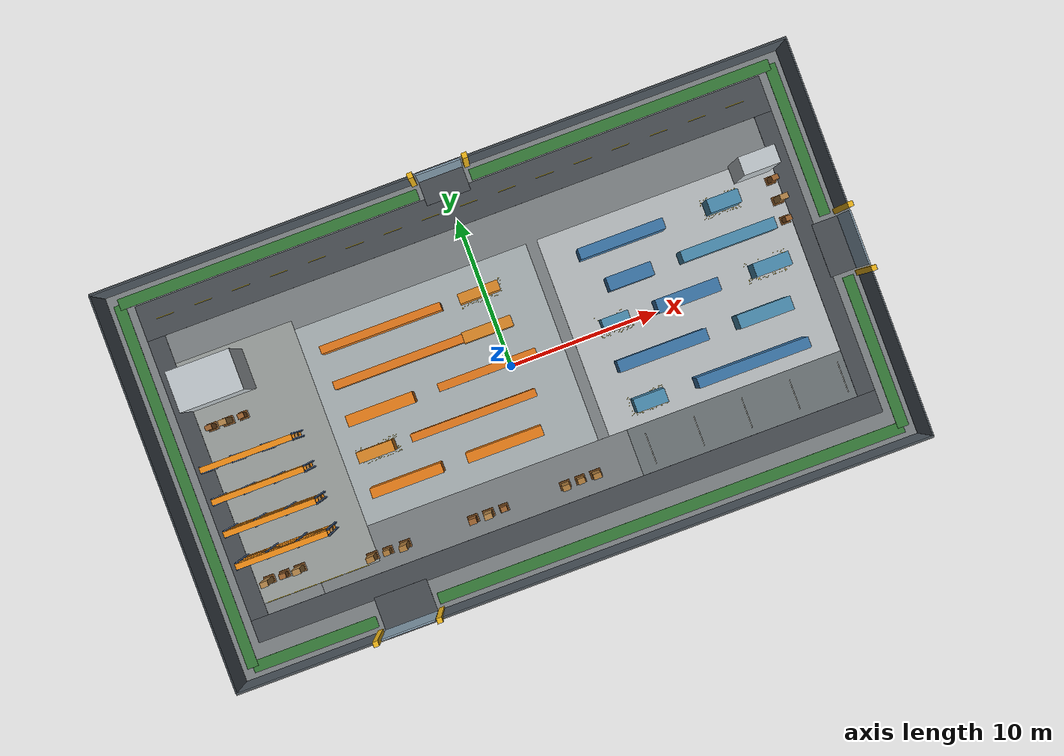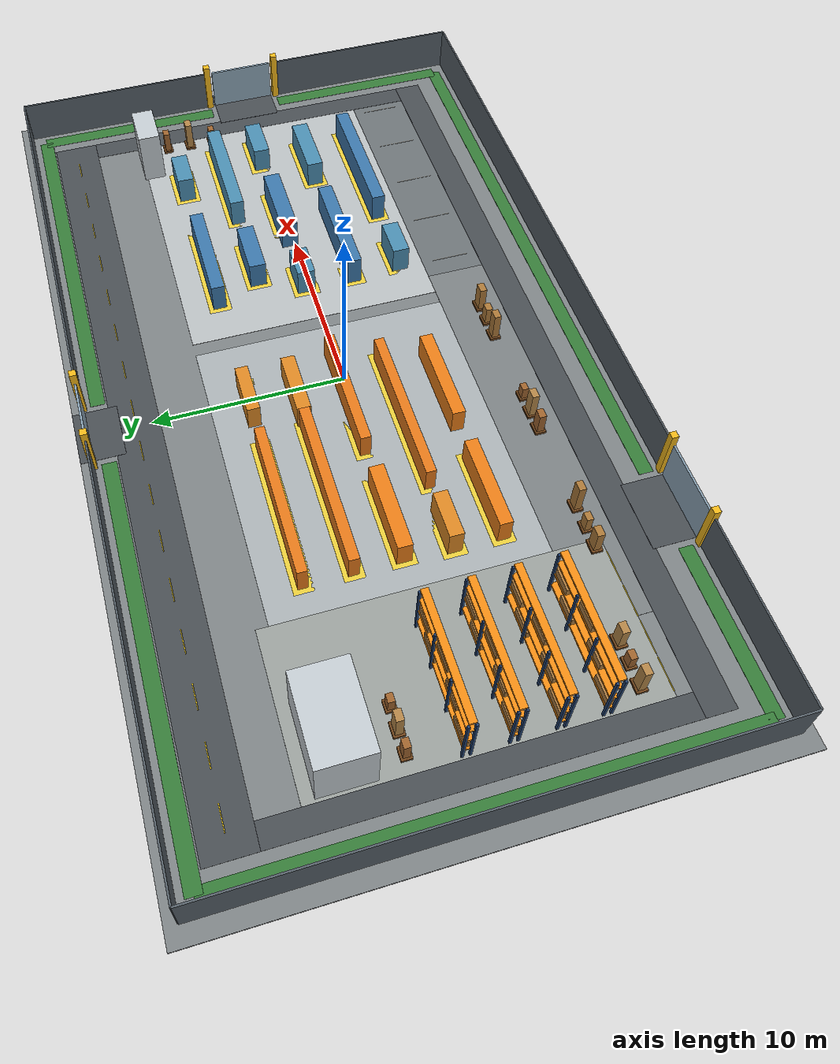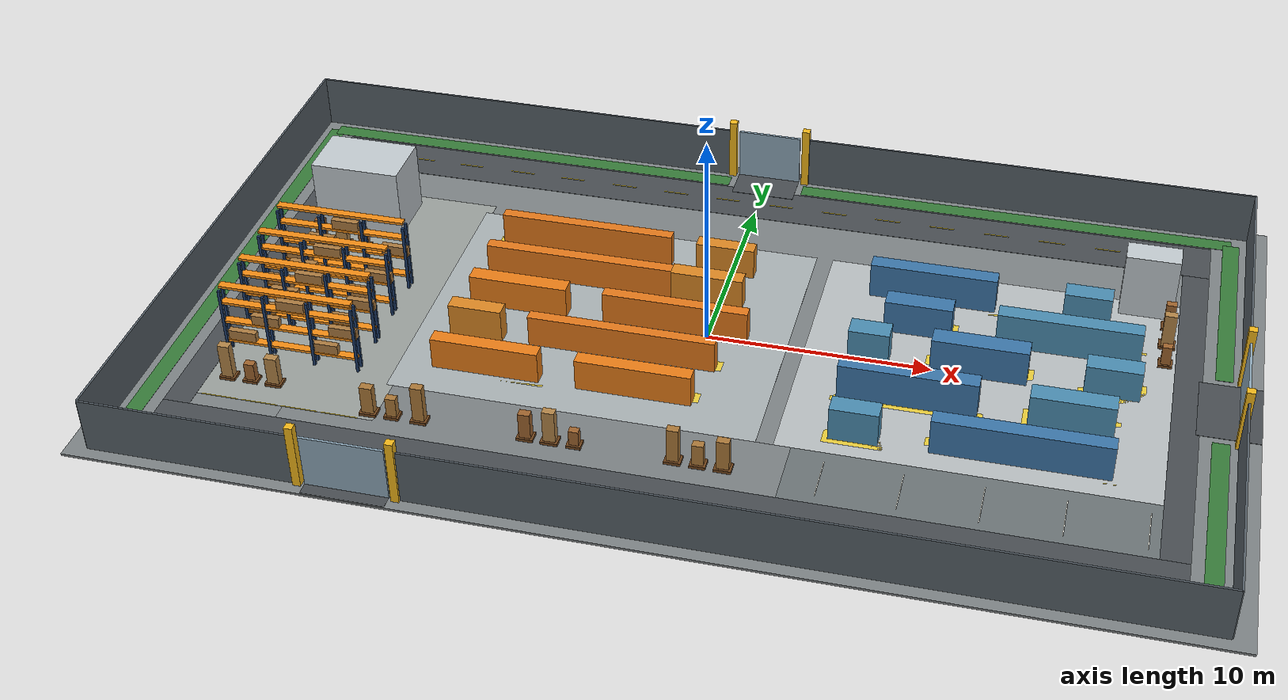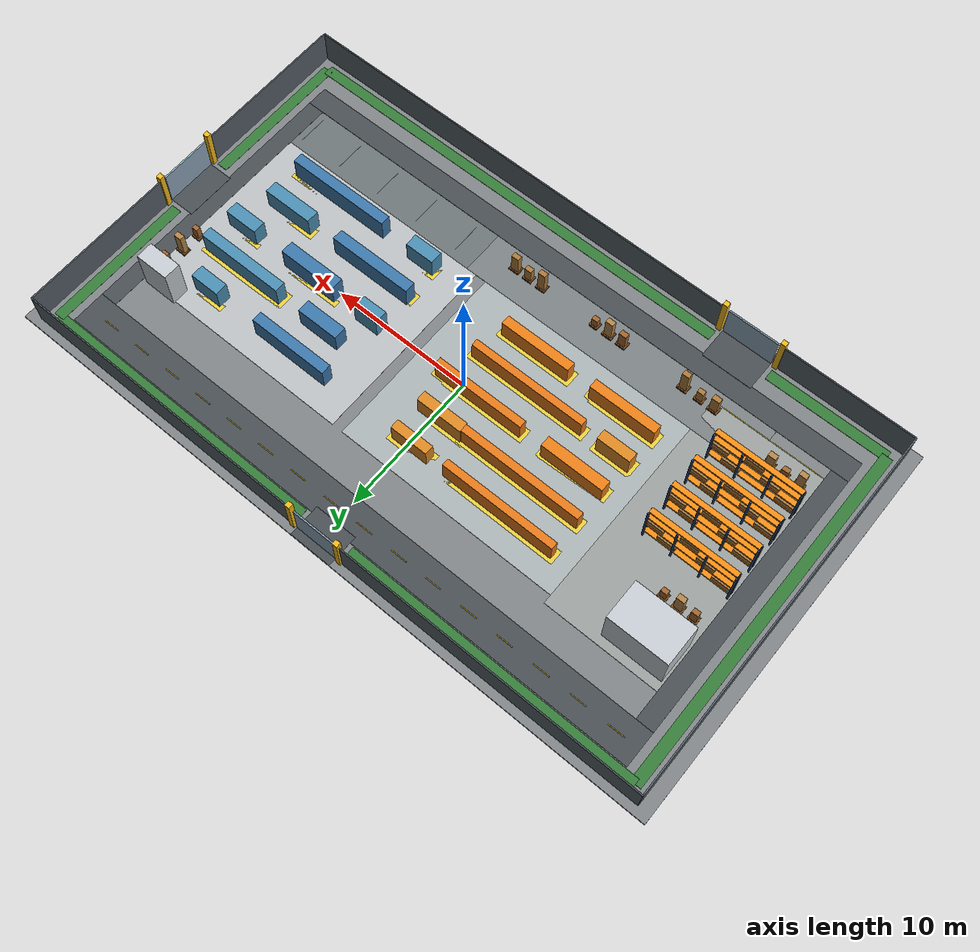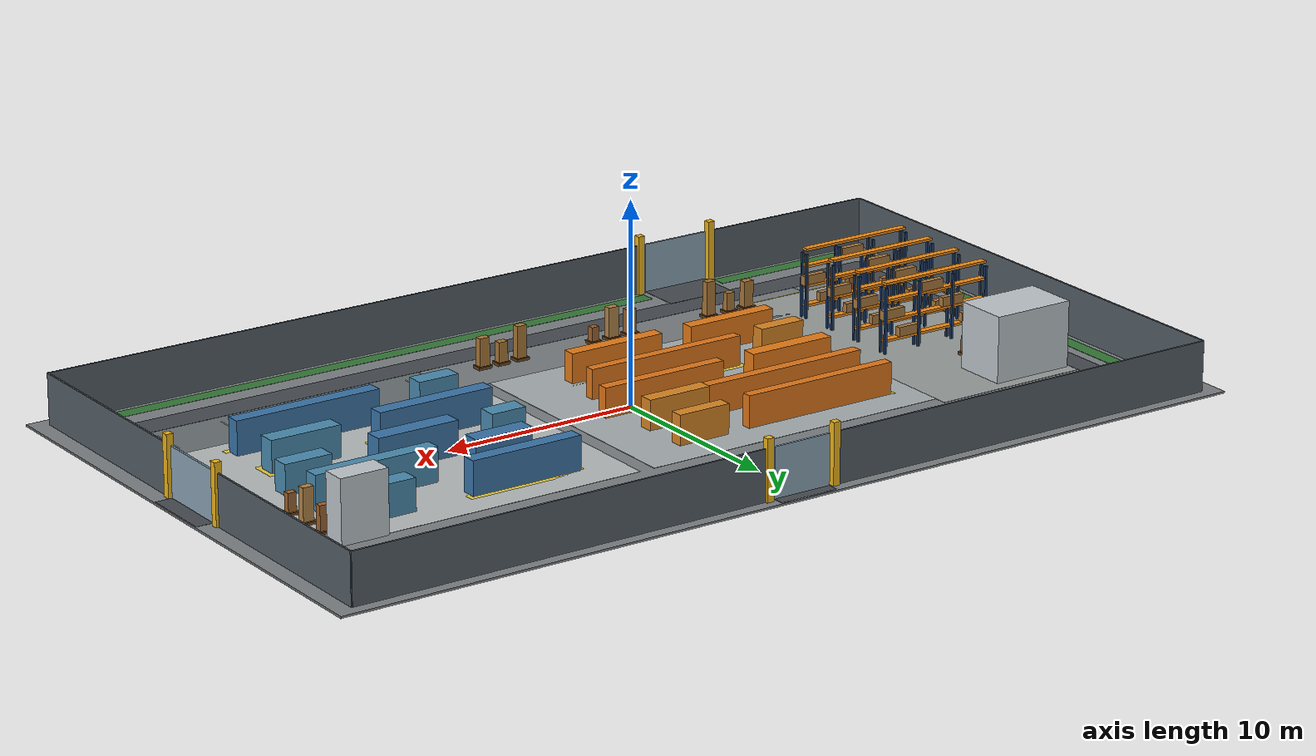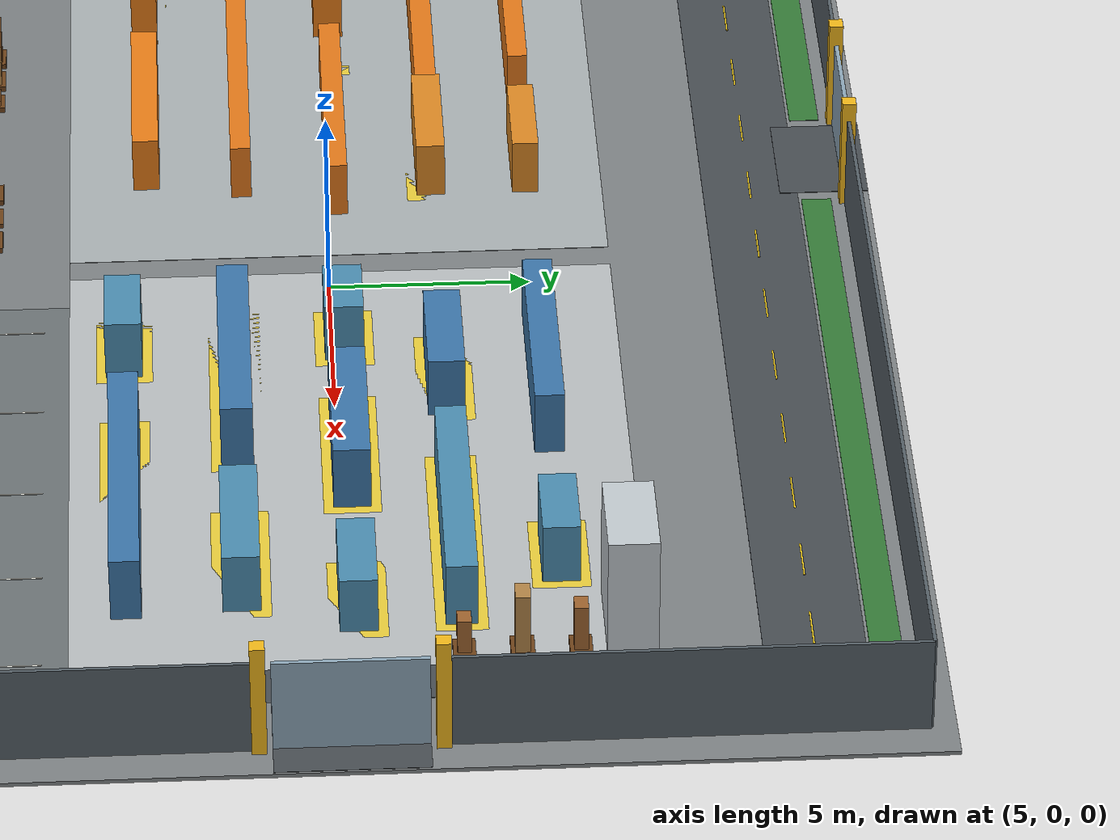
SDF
<?xml version="1.0" ?>
<sdf version="1.7">
  <world name="crtt_layout_demo">
    <gravity>0 0 -9.8</gravity>
    <plugin name="gazebo_ros_state" filename="libgazebo_ros_state.so">
      <ros><namespace>/gazebo</namespace></ros>
      <update_rate>10.0</update_rate>
    </plugin>
    <physics name="warehouse_physics" type="ode">
      <max_step_size>0.001</max_step_size>
      <real_time_factor>1.0</real_time_factor>
      <real_time_update_rate>1000</real_time_update_rate>
    </physics>
    <scene>
      <ambient>0.65 0.65 0.65 1</ambient>
      <background>0.72 0.76 0.80 1</background>
      <shadows>true</shadows>
    </scene>
    <gui fullscreen="0"><camera name="site_overview">
      <pose>0 -40 38 0 0.76 1.57</pose>
      <view_controller>orbit</view_controller>
    </camera></gui>
    <include><uri>model://sun</uri></include>

    <model name="site_floor">
      <static>true</static>
      <pose>0 0 -0.05 0 0 0</pose>
      <link name="floor">
        <collision name="collision"><geometry><box><size>48.0 27.599999999999998 0.10</size></box></geometry></collision>
        <visual name="visual">
          <geometry><box><size>48.0 27.599999999999998 0.10</size></box></geometry>
          <material><ambient>0.49 0.51 0.52 1</ambient><diffuse>0.49 0.51 0.52 1</diffuse></material>
        </visual>
      </link>
    </model>
    <model name="west_loading">
      <static>true</static>
      <pose>-16.8 -0.6 0.012 0 0 0</pose>
      <link name="marking">
        <visual name="visual">
          <geometry><box><size>9.0 16.5 0.012</size></box></geometry>

          <material>
            <ambient>0.60 0.62 0.61 1</ambient>
            <diffuse>0.60 0.62 0.61 1</diffuse>
          </material>
        </visual>
      </link>
    </model>
    <model name="central_production">
      <static>true</static>
      <pose>-4.5 0.3 0.012 0 0 0</pose>
      <link name="marking">
        <visual name="visual">
          <geometry><box><size>16.2 13.5 0.012</size></box></geometry>

          <material>
            <ambient>0.66 0.69 0.70 1</ambient>
            <diffuse>0.66 0.69 0.70 1</diffuse>
          </material>
        </visual>
      </link>
    </model>
    <model name="east_fabrication">
      <static>true</static>
      <pose>12.6 0.3 0.012 0 0 0</pose>
      <link name="marking">
        <visual name="visual">
          <geometry><box><size>16.5 13.5 0.012</size></box></geometry>

          <material>
            <ambient>0.72 0.74 0.75 1</ambient>
            <diffuse>0.72 0.74 0.75 1</diffuse>
          </material>
        </visual>
      </link>
    </model>
    <model name="south_service_pad">
      <static>true</static>
      <pose>-5.3999999999999995 -8.7 0.012 0 0 0</pose>
      <link name="marking">
        <visual name="visual">
          <geometry><box><size>21.9 4.5 0.012</size></box></geometry>

          <material>
            <ambient>0.48 0.50 0.51 1</ambient>
            <diffuse>0.48 0.50 0.51 1</diffuse>
          </material>
        </visual>
      </link>
    </model>
    <model name="southeast_parking">
      <static>true</static>
      <pose>12.9 -8.7 0.012 0 0 0</pose>
      <link name="marking">
        <visual name="visual">
          <geometry><box><size>15.6 4.5 0.012</size></box></geometry>

          <material>
            <ambient>0.42 0.45 0.46 1</ambient>
            <diffuse>0.42 0.45 0.46 1</diffuse>
          </material>
        </visual>
      </link>
    </model>
    <model name="north_access_road">
      <static>true</static>
      <pose>0.0 10.799999999999999 0.025 0 0 0</pose>
      <link name="marking">
        <visual name="visual">
          <geometry><box><size>42.9 2.4 0.012</size></box></geometry>

          <material>
            <ambient>0.28 0.30 0.32 1</ambient>
            <diffuse>0.28 0.30 0.32 1</diffuse>
          </material>
        </visual>
      </link>
    </model>
    <model name="west_perimeter_path">
      <static>true</static>
      <pose>-20.849999999999998 0.0 0.025 0 0 0</pose>
      <link name="marking">
        <visual name="visual">
          <geometry><box><size>1.2 19.2 0.012</size></box></geometry>

          <material>
            <ambient>0.28 0.30 0.32 1</ambient>
            <diffuse>0.28 0.30 0.32 1</diffuse>
          </material>
        </visual>
      </link>
    </model>
    <model name="east_perimeter_path">
      <static>true</static>
      <pose>20.849999999999998 0.0 0.025 0 0 0</pose>
      <link name="marking">
        <visual name="visual">
          <geometry><box><size>1.2 19.2 0.012</size></box></geometry>

          <material>
            <ambient>0.28 0.30 0.32 1</ambient>
            <diffuse>0.28 0.30 0.32 1</diffuse>
          </material>
        </visual>
      </link>
    </model>
    <model name="south_perimeter_path">
      <static>true</static>
      <pose>0.0 -10.35 0.025 0 0 0</pose>
      <link name="marking">
        <visual name="visual">
          <geometry><box><size>42.9 1.5 0.012</size></box></geometry>

          <material>
            <ambient>0.28 0.30 0.32 1</ambient>
            <diffuse>0.28 0.30 0.32 1</diffuse>
          </material>
        </visual>
      </link>
    </model>
    <model name="green_north_west">
      <static>true</static>
      <pose>-12.075 12.45 0.036 0 0 0</pose>
      <link name="marking">
        <visual name="visual">
          <geometry><box><size>20.55 0.75 0.012</size></box></geometry>

          <material>
            <ambient>0.21 0.48 0.22 1</ambient>
            <diffuse>0.21 0.48 0.22 1</diffuse>
          </material>
        </visual>
      </link>
    </model>
    <model name="green_north_east">
      <static>true</static>
      <pose>12.075 12.45 0.036 0 0 0</pose>
      <link name="marking">
        <visual name="visual">
          <geometry><box><size>20.55 0.75 0.012</size></box></geometry>

          <material>
            <ambient>0.21 0.48 0.22 1</ambient>
            <diffuse>0.21 0.48 0.22 1</diffuse>
          </material>
        </visual>
      </link>
    </model>
    <model name="green_west_edge">
      <static>true</static>
      <pose>-22.349999999999998 0.0 0.036 0 0 0</pose>
      <link name="marking">
        <visual name="visual">
          <geometry><box><size>0.75 24.9 0.012</size></box></geometry>

          <material>
            <ambient>0.21 0.48 0.22 1</ambient>
            <diffuse>0.21 0.48 0.22 1</diffuse>
          </material>
        </visual>
      </link>
    </model>
    <model name="green_east_north">
      <static>true</static>
      <pose>22.349999999999998 7.2749999999999995 0.036 0 0 0</pose>
      <link name="marking">
        <visual name="visual">
          <geometry><box><size>0.75 10.35 0.012</size></box></geometry>

          <material>
            <ambient>0.21 0.48 0.22 1</ambient>
            <diffuse>0.21 0.48 0.22 1</diffuse>
          </material>
        </visual>
      </link>
    </model>
    <model name="green_east_south">
      <static>true</static>
      <pose>22.349999999999998 -7.2749999999999995 0.036 0 0 0</pose>
      <link name="marking">
        <visual name="visual">
          <geometry><box><size>0.75 10.35 0.012</size></box></geometry>

          <material>
            <ambient>0.21 0.48 0.22 1</ambient>
            <diffuse>0.21 0.48 0.22 1</diffuse>
          </material>
        </visual>
      </link>
    </model>
    <model name="green_south_west">
      <static>true</static>
      <pose>-18.075 -12.45 0.036 0 0 0</pose>
      <link name="marking">
        <visual name="visual">
          <geometry><box><size>8.549999999999999 0.75 0.012</size></box></geometry>

          <material>
            <ambient>0.21 0.48 0.22 1</ambient>
            <diffuse>0.21 0.48 0.22 1</diffuse>
          </material>
        </visual>
      </link>
    </model>
    <model name="green_south_east">
      <static>true</static>
      <pose>6.375 -12.45 0.036 0 0 0</pose>
      <link name="marking">
        <visual name="visual">
          <geometry><box><size>31.95 0.75 0.012</size></box></geometry>

          <material>
            <ambient>0.21 0.48 0.22 1</ambient>
            <diffuse>0.21 0.48 0.22 1</diffuse>
          </material>
        </visual>
      </link>
    </model>
    <model name="north_entry_road">
      <static>true</static>
      <pose>0.0 12.674999999999999 0.05 0 0 0</pose>
      <link name="marking">
        <visual name="visual">
          <geometry><box><size>3.0 2.25 0.012</size></box></geometry>

          <material>
            <ambient>0.28 0.30 0.32 1</ambient>
            <diffuse>0.28 0.30 0.32 1</diffuse>
          </material>
        </visual>
      </link>
    </model>
    <model name="east_entry_road">
      <static>true</static>
      <pose>22.65 0.0 0.05 0 0 0</pose>
      <link name="marking">
        <visual name="visual">
          <geometry><box><size>2.6999999999999997 3.5999999999999996 0.012</size></box></geometry>

          <material>
            <ambient>0.28 0.30 0.32 1</ambient>
            <diffuse>0.28 0.30 0.32 1</diffuse>
          </material>
        </visual>
      </link>
    </model>
    <model name="south_loading_entry_road">
      <static>true</static>
      <pose>-11.7 -12.375 0.05 0 0 0</pose>
      <link name="marking">
        <visual name="visual">
          <geometry><box><size>3.5999999999999996 2.85 0.012</size></box></geometry>

          <material>
            <ambient>0.28 0.30 0.32 1</ambient>
            <diffuse>0.28 0.30 0.32 1</diffuse>
          </material>
        </visual>
      </link>
    </model>
    <model name="north_fence_west">
      <static>true</static>
      <pose>-12.45 13.2 1.25 0 0 0</pose>
      <link name="link">
        <collision name="collision">
          <geometry><box><size>21.3 0.09 2.5</size></box></geometry>
          <surface><friction><ode><mu>0.9</mu><mu2>0.9</mu2></ode></friction></surface>
        </collision>
        <visual name="visual">
          <geometry><box><size>21.3 0.09 2.5</size></box></geometry>

          <material>
            <ambient>0.33 0.37 0.40 1</ambient>
            <diffuse>0.33 0.37 0.40 1</diffuse>
          </material>
        </visual>
      </link>
    </model>
    <model name="north_fence_east">
      <static>true</static>
      <pose>12.45 13.2 1.25 0 0 0</pose>
      <link name="link">
        <collision name="collision">
          <geometry><box><size>21.3 0.09 2.5</size></box></geometry>
          <surface><friction><ode><mu>0.9</mu><mu2>0.9</mu2></ode></friction></surface>
        </collision>
        <visual name="visual">
          <geometry><box><size>21.3 0.09 2.5</size></box></geometry>

          <material>
            <ambient>0.33 0.37 0.40 1</ambient>
            <diffuse>0.33 0.37 0.40 1</diffuse>
          </material>
        </visual>
      </link>
    </model>
    <model name="south_fence_west">
      <static>true</static>
      <pose>-18.45 -13.2 1.25 0 0 0</pose>
      <link name="link">
        <collision name="collision">
          <geometry><box><size>9.299999999999999 0.09 2.5</size></box></geometry>
          <surface><friction><ode><mu>0.9</mu><mu2>0.9</mu2></ode></friction></surface>
        </collision>
        <visual name="visual">
          <geometry><box><size>9.299999999999999 0.09 2.5</size></box></geometry>

          <material>
            <ambient>0.33 0.37 0.40 1</ambient>
            <diffuse>0.33 0.37 0.40 1</diffuse>
          </material>
        </visual>
      </link>
    </model>
    <model name="south_fence_east">
      <static>true</static>
      <pose>6.75 -13.2 1.25 0 0 0</pose>
      <link name="link">
        <collision name="collision">
          <geometry><box><size>32.699999999999996 0.09 2.5</size></box></geometry>
          <surface><friction><ode><mu>0.9</mu><mu2>0.9</mu2></ode></friction></surface>
        </collision>
        <visual name="visual">
          <geometry><box><size>32.699999999999996 0.09 2.5</size></box></geometry>

          <material>
            <ambient>0.33 0.37 0.40 1</ambient>
            <diffuse>0.33 0.37 0.40 1</diffuse>
          </material>
        </visual>
      </link>
    </model>
    <model name="west_fence">
      <static>true</static>
      <pose>-23.099999999999998 0.0 1.25 0 0 0</pose>
      <link name="link">
        <collision name="collision">
          <geometry><box><size>0.09 26.4 2.5</size></box></geometry>
          <surface><friction><ode><mu>0.9</mu><mu2>0.9</mu2></ode></friction></surface>
        </collision>
        <visual name="visual">
          <geometry><box><size>0.09 26.4 2.5</size></box></geometry>

          <material>
            <ambient>0.33 0.37 0.40 1</ambient>
            <diffuse>0.33 0.37 0.40 1</diffuse>
          </material>
        </visual>
      </link>
    </model>
    <model name="east_fence_south">
      <static>true</static>
      <pose>23.099999999999998 -7.6499999999999995 1.25 0 0 0</pose>
      <link name="link">
        <collision name="collision">
          <geometry><box><size>0.09 11.1 2.5</size></box></geometry>
          <surface><friction><ode><mu>0.9</mu><mu2>0.9</mu2></ode></friction></surface>
        </collision>
        <visual name="visual">
          <geometry><box><size>0.09 11.1 2.5</size></box></geometry>

          <material>
            <ambient>0.33 0.37 0.40 1</ambient>
            <diffuse>0.33 0.37 0.40 1</diffuse>
          </material>
        </visual>
      </link>
    </model>
    <model name="east_fence_north">
      <static>true</static>
      <pose>23.099999999999998 7.6499999999999995 1.25 0 0 0</pose>
      <link name="link">
        <collision name="collision">
          <geometry><box><size>0.09 11.1 2.5</size></box></geometry>
          <surface><friction><ode><mu>0.9</mu><mu2>0.9</mu2></ode></friction></surface>
        </collision>
        <visual name="visual">
          <geometry><box><size>0.09 11.1 2.5</size></box></geometry>

          <material>
            <ambient>0.33 0.37 0.40 1</ambient>
            <diffuse>0.33 0.37 0.40 1</diffuse>
          </material>
        </visual>
      </link>
    </model>
    <model name="loading_office">
      <static>true</static>
      <pose>-18.0 5.7 1.65 0 0 0</pose>
      <link name="link">
        <collision name="collision">
          <geometry><box><size>4.2 2.6999999999999997 3.3</size></box></geometry>
          <surface><friction><ode><mu>0.9</mu><mu2>0.9</mu2></ode></friction></surface>
        </collision>
        <visual name="visual">
          <geometry><box><size>4.2 2.6999999999999997 3.3</size></box></geometry>

          <material>
            <ambient>0.76 0.79 0.81 1</ambient>
            <diffuse>0.76 0.79 0.81 1</diffuse>
          </material>
        </visual>
      </link>
    </model>
    <model name="northeast_service_building">
      <static>true</static>
      <pose>18.75 6.6 1.55 0 0 0</pose>
      <link name="link">
        <collision name="collision">
          <geometry><box><size>2.4 1.2 3.1</size></box></geometry>
          <surface><friction><ode><mu>0.9</mu><mu2>0.9</mu2></ode></friction></surface>
        </collision>
        <visual name="visual">
          <geometry><box><size>2.4 1.2 3.1</size></box></geometry>

          <material>
            <ambient>0.76 0.79 0.81 1</ambient>
            <diffuse>0.76 0.79 0.81 1</diffuse>
          </material>
        </visual>
      </link>
    </model>
    <model name="west_rack_1">
      <static>true</static>
      <pose>-17.099999999999998 -5.7 0 0 0 0</pose>
      <link name="rack">
        <collision name="rack_footprint">
          <pose>0 0 1.65 0 0 0</pose>
          <geometry><box><size>6.0 0.36 3.3</size></box></geometry>
        </collision>

        <visual name="upright_0_0">
          <pose>-3.0 -0.18 1.65 0 0 0</pose>
          <geometry><box><size>0.12 0.12 3.3</size></box></geometry>

          <material>
            <ambient>0.12 0.24 0.42 1</ambient>
            <diffuse>0.12 0.24 0.42 1</diffuse>
          </material>
        </visual>
        <visual name="upright_0_1">
          <pose>-3.0 0.18 1.65 0 0 0</pose>
          <geometry><box><size>0.12 0.12 3.3</size></box></geometry>

          <material>
            <ambient>0.12 0.24 0.42 1</ambient>
            <diffuse>0.12 0.24 0.42 1</diffuse>
          </material>
        </visual>
        <visual name="upright_1_0">
          <pose>-1.0 -0.18 1.65 0 0 0</pose>
          <geometry><box><size>0.12 0.12 3.3</size></box></geometry>

          <material>
            <ambient>0.12 0.24 0.42 1</ambient>
            <diffuse>0.12 0.24 0.42 1</diffuse>
          </material>
        </visual>
        <visual name="upright_1_1">
          <pose>-1.0 0.18 1.65 0 0 0</pose>
          <geometry><box><size>0.12 0.12 3.3</size></box></geometry>

          <material>
            <ambient>0.12 0.24 0.42 1</ambient>
            <diffuse>0.12 0.24 0.42 1</diffuse>
          </material>
        </visual>
        <visual name="upright_2_0">
          <pose>1.0 -0.18 1.65 0 0 0</pose>
          <geometry><box><size>0.12 0.12 3.3</size></box></geometry>

          <material>
            <ambient>0.12 0.24 0.42 1</ambient>
            <diffuse>0.12 0.24 0.42 1</diffuse>
          </material>
        </visual>
        <visual name="upright_2_1">
          <pose>1.0 0.18 1.65 0 0 0</pose>
          <geometry><box><size>0.12 0.12 3.3</size></box></geometry>

          <material>
            <ambient>0.12 0.24 0.42 1</ambient>
            <diffuse>0.12 0.24 0.42 1</diffuse>
          </material>
        </visual>
        <visual name="upright_3_0">
          <pose>3.0 -0.18 1.65 0 0 0</pose>
          <geometry><box><size>0.12 0.12 3.3</size></box></geometry>

          <material>
            <ambient>0.12 0.24 0.42 1</ambient>
            <diffuse>0.12 0.24 0.42 1</diffuse>
          </material>
        </visual>
        <visual name="upright_3_1">
          <pose>3.0 0.18 1.65 0 0 0</pose>
          <geometry><box><size>0.12 0.12 3.3</size></box></geometry>

          <material>
            <ambient>0.12 0.24 0.42 1</ambient>
            <diffuse>0.12 0.24 0.42 1</diffuse>
          </material>
        </visual>
        <visual name="beam_0">
          <pose>0 0 0.65 0 0 0</pose>
          <geometry><box><size>6.0 0.36 0.12</size></box></geometry>

          <material>
            <ambient>0.95 0.55 0.08 1</ambient>
            <diffuse>0.95 0.55 0.08 1</diffuse>
          </material>
        </visual>
        <visual name="beam_1">
          <pose>0 0 1.65 0 0 0</pose>
          <geometry><box><size>6.0 0.36 0.12</size></box></geometry>

          <material>
            <ambient>0.95 0.55 0.08 1</ambient>
            <diffuse>0.95 0.55 0.08 1</diffuse>
          </material>
        </visual>
        <visual name="beam_2">
          <pose>0 0 2.65 0 0 0</pose>
          <geometry><box><size>6.0 0.36 0.12</size></box></geometry>

          <material>
            <ambient>0.95 0.55 0.08 1</ambient>
            <diffuse>0.95 0.55 0.08 1</diffuse>
          </material>
        </visual>
        <visual name="beam_3">
          <pose>0 0 3.5 0 0 0</pose>
          <geometry><box><size>6.0 0.36 0.12</size></box></geometry>

          <material>
            <ambient>0.95 0.55 0.08 1</ambient>
            <diffuse>0.95 0.55 0.08 1</diffuse>
          </material>
        </visual>
        <visual name="load_0">
          <pose>-2.2800000000000002 0 0.92 0 0 0</pose>
          <geometry><box><size>1.25 0.2808 0.48</size></box></geometry>

          <material>
            <ambient>0.67 0.48 0.25 1</ambient>
            <diffuse>0.67 0.48 0.25 1</diffuse>
          </material>
        </visual>
        <visual name="load_1">
          <pose>-1.08 0 1.92 0 0 0</pose>
          <geometry><box><size>1.25 0.2808 0.48</size></box></geometry>

          <material>
            <ambient>0.67 0.48 0.25 1</ambient>
            <diffuse>0.67 0.48 0.25 1</diffuse>
          </material>
        </visual>
        <visual name="load_2">
          <pose>0.18 0 2.92 0 0 0</pose>
          <geometry><box><size>1.25 0.2808 0.48</size></box></geometry>

          <material>
            <ambient>0.67 0.48 0.25 1</ambient>
            <diffuse>0.67 0.48 0.25 1</diffuse>
          </material>
        </visual>
        <visual name="load_3">
          <pose>1.5 0 0.92 0 0 0</pose>
          <geometry><box><size>1.25 0.2808 0.48</size></box></geometry>

          <material>
            <ambient>0.67 0.48 0.25 1</ambient>
            <diffuse>0.67 0.48 0.25 1</diffuse>
          </material>
        </visual>
        <visual name="load_4">
          <pose>2.46 0 1.92 0 0 0</pose>
          <geometry><box><size>1.25 0.2808 0.48</size></box></geometry>

          <material>
            <ambient>0.67 0.48 0.25 1</ambient>
            <diffuse>0.67 0.48 0.25 1</diffuse>
          </material>
        </visual>
      </link>
    </model>
    <model name="west_rack_2">
      <static>true</static>
      <pose>-17.099999999999998 -3.5999999999999996 0 0 0 0</pose>
      <link name="rack">
        <collision name="rack_footprint">
          <pose>0 0 1.65 0 0 0</pose>
          <geometry><box><size>6.0 0.36 3.3</size></box></geometry>
        </collision>

        <visual name="upright_0_0">
          <pose>-3.0 -0.18 1.65 0 0 0</pose>
          <geometry><box><size>0.12 0.12 3.3</size></box></geometry>

          <material>
            <ambient>0.12 0.24 0.42 1</ambient>
            <diffuse>0.12 0.24 0.42 1</diffuse>
          </material>
        </visual>
        <visual name="upright_0_1">
          <pose>-3.0 0.18 1.65 0 0 0</pose>
          <geometry><box><size>0.12 0.12 3.3</size></box></geometry>

          <material>
            <ambient>0.12 0.24 0.42 1</ambient>
            <diffuse>0.12 0.24 0.42 1</diffuse>
          </material>
        </visual>
        <visual name="upright_1_0">
          <pose>-1.0 -0.18 1.65 0 0 0</pose>
          <geometry><box><size>0.12 0.12 3.3</size></box></geometry>

          <material>
            <ambient>0.12 0.24 0.42 1</ambient>
            <diffuse>0.12 0.24 0.42 1</diffuse>
          </material>
        </visual>
        <visual name="upright_1_1">
          <pose>-1.0 0.18 1.65 0 0 0</pose>
          <geometry><box><size>0.12 0.12 3.3</size></box></geometry>

          <material>
            <ambient>0.12 0.24 0.42 1</ambient>
            <diffuse>0.12 0.24 0.42 1</diffuse>
          </material>
        </visual>
        <visual name="upright_2_0">
          <pose>1.0 -0.18 1.65 0 0 0</pose>
          <geometry><box><size>0.12 0.12 3.3</size></box></geometry>

          <material>
            <ambient>0.12 0.24 0.42 1</ambient>
            <diffuse>0.12 0.24 0.42 1</diffuse>
          </material>
        </visual>
        <visual name="upright_2_1">
          <pose>1.0 0.18 1.65 0 0 0</pose>
          <geometry><box><size>0.12 0.12 3.3</size></box></geometry>

          <material>
            <ambient>0.12 0.24 0.42 1</ambient>
            <diffuse>0.12 0.24 0.42 1</diffuse>
          </material>
        </visual>
        <visual name="upright_3_0">
          <pose>3.0 -0.18 1.65 0 0 0</pose>
          <geometry><box><size>0.12 0.12 3.3</size></box></geometry>

          <material>
            <ambient>0.12 0.24 0.42 1</ambient>
            <diffuse>0.12 0.24 0.42 1</diffuse>
          </material>
        </visual>
        <visual name="upright_3_1">
          <pose>3.0 0.18 1.65 0 0 0</pose>
          <geometry><box><size>0.12 0.12 3.3</size></box></geometry>

          <material>
            <ambient>0.12 0.24 0.42 1</ambient>
            <diffuse>0.12 0.24 0.42 1</diffuse>
          </material>
        </visual>
        <visual name="beam_0">
          <pose>0 0 0.65 0 0 0</pose>
          <geometry><box><size>6.0 0.36 0.12</size></box></geometry>

          <material>
            <ambient>0.95 0.55 0.08 1</ambient>
            <diffuse>0.95 0.55 0.08 1</diffuse>
          </material>
        </visual>
        <visual name="beam_1">
          <pose>0 0 1.65 0 0 0</pose>
          <geometry><box><size>6.0 0.36 0.12</size></box></geometry>

          <material>
            <ambient>0.95 0.55 0.08 1</ambient>
            <diffuse>0.95 0.55 0.08 1</diffuse>
          </material>
        </visual>
        <visual name="beam_2">
          <pose>0 0 2.65 0 0 0</pose>
          <geometry><box><size>6.0 0.36 0.12</size></box></geometry>

          <material>
            <ambient>0.95 0.55 0.08 1</ambient>
            <diffuse>0.95 0.55 0.08 1</diffuse>
          </material>
        </visual>
        <visual name="beam_3">
          <pose>0 0 3.5 0 0 0</pose>
          <geometry><box><size>6.0 0.36 0.12</size></box></geometry>

          <material>
            <ambient>0.95 0.55 0.08 1</ambient>
            <diffuse>0.95 0.55 0.08 1</diffuse>
          </material>
        </visual>
        <visual name="load_0">
          <pose>-2.2800000000000002 0 0.92 0 0 0</pose>
          <geometry><box><size>1.25 0.2808 0.48</size></box></geometry>

          <material>
            <ambient>0.67 0.48 0.25 1</ambient>
            <diffuse>0.67 0.48 0.25 1</diffuse>
          </material>
        </visual>
        <visual name="load_1">
          <pose>-1.08 0 1.92 0 0 0</pose>
          <geometry><box><size>1.25 0.2808 0.48</size></box></geometry>

          <material>
            <ambient>0.67 0.48 0.25 1</ambient>
            <diffuse>0.67 0.48 0.25 1</diffuse>
          </material>
        </visual>
        <visual name="load_2">
          <pose>0.18 0 2.92 0 0 0</pose>
          <geometry><box><size>1.25 0.2808 0.48</size></box></geometry>

          <material>
            <ambient>0.67 0.48 0.25 1</ambient>
            <diffuse>0.67 0.48 0.25 1</diffuse>
          </material>
        </visual>
        <visual name="load_3">
          <pose>1.5 0 0.92 0 0 0</pose>
          <geometry><box><size>1.25 0.2808 0.48</size></box></geometry>

          <material>
            <ambient>0.67 0.48 0.25 1</ambient>
            <diffuse>0.67 0.48 0.25 1</diffuse>
          </material>
        </visual>
        <visual name="load_4">
          <pose>2.46 0 1.92 0 0 0</pose>
          <geometry><box><size>1.25 0.2808 0.48</size></box></geometry>

          <material>
            <ambient>0.67 0.48 0.25 1</ambient>
            <diffuse>0.67 0.48 0.25 1</diffuse>
          </material>
        </visual>
      </link>
    </model>
    <model name="west_rack_3">
      <static>true</static>
      <pose>-17.099999999999998 -1.5 0 0 0 0</pose>
      <link name="rack">
        <collision name="rack_footprint">
          <pose>0 0 1.65 0 0 0</pose>
          <geometry><box><size>6.0 0.36 3.3</size></box></geometry>
        </collision>

        <visual name="upright_0_0">
          <pose>-3.0 -0.18 1.65 0 0 0</pose>
          <geometry><box><size>0.12 0.12 3.3</size></box></geometry>

          <material>
            <ambient>0.12 0.24 0.42 1</ambient>
            <diffuse>0.12 0.24 0.42 1</diffuse>
          </material>
        </visual>
        <visual name="upright_0_1">
          <pose>-3.0 0.18 1.65 0 0 0</pose>
          <geometry><box><size>0.12 0.12 3.3</size></box></geometry>

          <material>
            <ambient>0.12 0.24 0.42 1</ambient>
            <diffuse>0.12 0.24 0.42 1</diffuse>
          </material>
        </visual>
        <visual name="upright_1_0">
          <pose>-1.0 -0.18 1.65 0 0 0</pose>
          <geometry><box><size>0.12 0.12 3.3</size></box></geometry>

          <material>
            <ambient>0.12 0.24 0.42 1</ambient>
            <diffuse>0.12 0.24 0.42 1</diffuse>
          </material>
        </visual>
        <visual name="upright_1_1">
          <pose>-1.0 0.18 1.65 0 0 0</pose>
          <geometry><box><size>0.12 0.12 3.3</size></box></geometry>

          <material>
            <ambient>0.12 0.24 0.42 1</ambient>
            <diffuse>0.12 0.24 0.42 1</diffuse>
          </material>
        </visual>
        <visual name="upright_2_0">
          <pose>1.0 -0.18 1.65 0 0 0</pose>
          <geometry><box><size>0.12 0.12 3.3</size></box></geometry>

          <material>
            <ambient>0.12 0.24 0.42 1</ambient>
            <diffuse>0.12 0.24 0.42 1</diffuse>
          </material>
        </visual>
        <visual name="upright_2_1">
          <pose>1.0 0.18 1.65 0 0 0</pose>
          <geometry><box><size>0.12 0.12 3.3</size></box></geometry>

          <material>
            <ambient>0.12 0.24 0.42 1</ambient>
            <diffuse>0.12 0.24 0.42 1</diffuse>
          </material>
        </visual>
        <visual name="upright_3_0">
          <pose>3.0 -0.18 1.65 0 0 0</pose>
          <geometry><box><size>0.12 0.12 3.3</size></box></geometry>

          <material>
            <ambient>0.12 0.24 0.42 1</ambient>
            <diffuse>0.12 0.24 0.42 1</diffuse>
          </material>
        </visual>
        <visual name="upright_3_1">
          <pose>3.0 0.18 1.65 0 0 0</pose>
          <geometry><box><size>0.12 0.12 3.3</size></box></geometry>

          <material>
            <ambient>0.12 0.24 0.42 1</ambient>
            <diffuse>0.12 0.24 0.42 1</diffuse>
          </material>
        </visual>
        <visual name="beam_0">
          <pose>0 0 0.65 0 0 0</pose>
          <geometry><box><size>6.0 0.36 0.12</size></box></geometry>

          <material>
            <ambient>0.95 0.55 0.08 1</ambient>
            <diffuse>0.95 0.55 0.08 1</diffuse>
          </material>
        </visual>
        <visual name="beam_1">
          <pose>0 0 1.65 0 0 0</pose>
          <geometry><box><size>6.0 0.36 0.12</size></box></geometry>

          <material>
            <ambient>0.95 0.55 0.08 1</ambient>
            <diffuse>0.95 0.55 0.08 1</diffuse>
          </material>
        </visual>
        <visual name="beam_2">
          <pose>0 0 2.65 0 0 0</pose>
          <geometry><box><size>6.0 0.36 0.12</size></box></geometry>

          <material>
            <ambient>0.95 0.55 0.08 1</ambient>
            <diffuse>0.95 0.55 0.08 1</diffuse>
          </material>
        </visual>
        <visual name="beam_3">
          <pose>0 0 3.5 0 0 0</pose>
          <geometry><box><size>6.0 0.36 0.12</size></box></geometry>

          <material>
            <ambient>0.95 0.55 0.08 1</ambient>
            <diffuse>0.95 0.55 0.08 1</diffuse>
          </material>
        </visual>
        <visual name="load_0">
          <pose>-2.2800000000000002 0 0.92 0 0 0</pose>
          <geometry><box><size>1.25 0.2808 0.48</size></box></geometry>

          <material>
            <ambient>0.67 0.48 0.25 1</ambient>
            <diffuse>0.67 0.48 0.25 1</diffuse>
          </material>
        </visual>
        <visual name="load_1">
          <pose>-1.08 0 1.92 0 0 0</pose>
          <geometry><box><size>1.25 0.2808 0.48</size></box></geometry>

          <material>
            <ambient>0.67 0.48 0.25 1</ambient>
            <diffuse>0.67 0.48 0.25 1</diffuse>
          </material>
        </visual>
        <visual name="load_2">
          <pose>0.18 0 2.92 0 0 0</pose>
          <geometry><box><size>1.25 0.2808 0.48</size></box></geometry>

          <material>
            <ambient>0.67 0.48 0.25 1</ambient>
            <diffuse>0.67 0.48 0.25 1</diffuse>
          </material>
        </visual>
        <visual name="load_3">
          <pose>1.5 0 0.92 0 0 0</pose>
          <geometry><box><size>1.25 0.2808 0.48</size></box></geometry>

          <material>
            <ambient>0.67 0.48 0.25 1</ambient>
            <diffuse>0.67 0.48 0.25 1</diffuse>
          </material>
        </visual>
        <visual name="load_4">
          <pose>2.46 0 1.92 0 0 0</pose>
          <geometry><box><size>1.25 0.2808 0.48</size></box></geometry>

          <material>
            <ambient>0.67 0.48 0.25 1</ambient>
            <diffuse>0.67 0.48 0.25 1</diffuse>
          </material>
        </visual>
      </link>
    </model>
    <model name="west_rack_4">
      <static>true</static>
      <pose>-17.099999999999998 0.6 0 0 0 0</pose>
      <link name="rack">
        <collision name="rack_footprint">
          <pose>0 0 1.65 0 0 0</pose>
          <geometry><box><size>6.0 0.36 3.3</size></box></geometry>
        </collision>

        <visual name="upright_0_0">
          <pose>-3.0 -0.18 1.65 0 0 0</pose>
          <geometry><box><size>0.12 0.12 3.3</size></box></geometry>

          <material>
            <ambient>0.12 0.24 0.42 1</ambient>
            <diffuse>0.12 0.24 0.42 1</diffuse>
          </material>
        </visual>
        <visual name="upright_0_1">
          <pose>-3.0 0.18 1.65 0 0 0</pose>
          <geometry><box><size>0.12 0.12 3.3</size></box></geometry>

          <material>
            <ambient>0.12 0.24 0.42 1</ambient>
            <diffuse>0.12 0.24 0.42 1</diffuse>
          </material>
        </visual>
        <visual name="upright_1_0">
          <pose>-1.0 -0.18 1.65 0 0 0</pose>
          <geometry><box><size>0.12 0.12 3.3</size></box></geometry>

          <material>
            <ambient>0.12 0.24 0.42 1</ambient>
            <diffuse>0.12 0.24 0.42 1</diffuse>
          </material>
        </visual>
        <visual name="upright_1_1">
          <pose>-1.0 0.18 1.65 0 0 0</pose>
          <geometry><box><size>0.12 0.12 3.3</size></box></geometry>

          <material>
            <ambient>0.12 0.24 0.42 1</ambient>
            <diffuse>0.12 0.24 0.42 1</diffuse>
          </material>
        </visual>
        <visual name="upright_2_0">
          <pose>1.0 -0.18 1.65 0 0 0</pose>
          <geometry><box><size>0.12 0.12 3.3</size></box></geometry>

          <material>
            <ambient>0.12 0.24 0.42 1</ambient>
            <diffuse>0.12 0.24 0.42 1</diffuse>
          </material>
        </visual>
        <visual name="upright_2_1">
          <pose>1.0 0.18 1.65 0 0 0</pose>
          <geometry><box><size>0.12 0.12 3.3</size></box></geometry>

          <material>
            <ambient>0.12 0.24 0.42 1</ambient>
            <diffuse>0.12 0.24 0.42 1</diffuse>
          </material>
        </visual>
        <visual name="upright_3_0">
          <pose>3.0 -0.18 1.65 0 0 0</pose>
          <geometry><box><size>0.12 0.12 3.3</size></box></geometry>

          <material>
            <ambient>0.12 0.24 0.42 1</ambient>
            <diffuse>0.12 0.24 0.42 1</diffuse>
          </material>
        </visual>
        <visual name="upright_3_1">
          <pose>3.0 0.18 1.65 0 0 0</pose>
          <geometry><box><size>0.12 0.12 3.3</size></box></geometry>

          <material>
            <ambient>0.12 0.24 0.42 1</ambient>
            <diffuse>0.12 0.24 0.42 1</diffuse>
          </material>
        </visual>
        <visual name="beam_0">
          <pose>0 0 0.65 0 0 0</pose>
          <geometry><box><size>6.0 0.36 0.12</size></box></geometry>

          <material>
            <ambient>0.95 0.55 0.08 1</ambient>
            <diffuse>0.95 0.55 0.08 1</diffuse>
          </material>
        </visual>
        <visual name="beam_1">
          <pose>0 0 1.65 0 0 0</pose>
          <geometry><box><size>6.0 0.36 0.12</size></box></geometry>

          <material>
            <ambient>0.95 0.55 0.08 1</ambient>
            <diffuse>0.95 0.55 0.08 1</diffuse>
          </material>
        </visual>
        <visual name="beam_2">
          <pose>0 0 2.65 0 0 0</pose>
          <geometry><box><size>6.0 0.36 0.12</size></box></geometry>

          <material>
            <ambient>0.95 0.55 0.08 1</ambient>
            <diffuse>0.95 0.55 0.08 1</diffuse>
          </material>
        </visual>
        <visual name="beam_3">
          <pose>0 0 3.5 0 0 0</pose>
          <geometry><box><size>6.0 0.36 0.12</size></box></geometry>

          <material>
            <ambient>0.95 0.55 0.08 1</ambient>
            <diffuse>0.95 0.55 0.08 1</diffuse>
          </material>
        </visual>
        <visual name="load_0">
          <pose>-2.2800000000000002 0 0.92 0 0 0</pose>
          <geometry><box><size>1.25 0.2808 0.48</size></box></geometry>

          <material>
            <ambient>0.67 0.48 0.25 1</ambient>
            <diffuse>0.67 0.48 0.25 1</diffuse>
          </material>
        </visual>
        <visual name="load_1">
          <pose>-1.08 0 1.92 0 0 0</pose>
          <geometry><box><size>1.25 0.2808 0.48</size></box></geometry>

          <material>
            <ambient>0.67 0.48 0.25 1</ambient>
            <diffuse>0.67 0.48 0.25 1</diffuse>
          </material>
        </visual>
        <visual name="load_2">
          <pose>0.18 0 2.92 0 0 0</pose>
          <geometry><box><size>1.25 0.2808 0.48</size></box></geometry>

          <material>
            <ambient>0.67 0.48 0.25 1</ambient>
            <diffuse>0.67 0.48 0.25 1</diffuse>
          </material>
        </visual>
        <visual name="load_3">
          <pose>1.5 0 0.92 0 0 0</pose>
          <geometry><box><size>1.25 0.2808 0.48</size></box></geometry>

          <material>
            <ambient>0.67 0.48 0.25 1</ambient>
            <diffuse>0.67 0.48 0.25 1</diffuse>
          </material>
        </visual>
        <visual name="load_4">
          <pose>2.46 0 1.92 0 0 0</pose>
          <geometry><box><size>1.25 0.2808 0.48</size></box></geometry>

          <material>
            <ambient>0.67 0.48 0.25 1</ambient>
            <diffuse>0.67 0.48 0.25 1</diffuse>
          </material>
        </visual>
      </link>
    </model>
    <model name="north_gate_west_post">
      <static>true</static>
      <pose>-1.7999999999999998 13.2 1.5 0 0 0</pose>
      <link name="link">
        <collision name="collision">
          <geometry><box><size>0.35 0.35 3.0</size></box></geometry>
          <surface><friction><ode><mu>0.9</mu><mu2>0.9</mu2></ode></friction></surface>
        </collision>
        <visual name="visual">
          <geometry><box><size>0.35 0.35 3.0</size></box></geometry>

          <material>
            <ambient>0.95 0.72 0.10 1</ambient>
            <diffuse>0.95 0.72 0.10 1</diffuse>
          </material>
        </visual>
      </link>
    </model>
    <model name="north_gate_east_post">
      <static>true</static>
      <pose>1.7999999999999998 13.2 1.5 0 0 0</pose>
      <link name="link">
        <collision name="collision">
          <geometry><box><size>0.35 0.35 3.0</size></box></geometry>
          <surface><friction><ode><mu>0.9</mu><mu2>0.9</mu2></ode></friction></surface>
        </collision>
        <visual name="visual">
          <geometry><box><size>0.35 0.35 3.0</size></box></geometry>

          <material>
            <ambient>0.95 0.72 0.10 1</ambient>
            <diffuse>0.95 0.72 0.10 1</diffuse>
          </material>
        </visual>
      </link>
    </model>
    <model name="east_gate_south_post">
      <static>true</static>
      <pose>23.099999999999998 -2.1 1.5 0 0 0</pose>
      <link name="link">
        <collision name="collision">
          <geometry><box><size>0.35 0.35 3.0</size></box></geometry>
          <surface><friction><ode><mu>0.9</mu><mu2>0.9</mu2></ode></friction></surface>
        </collision>
        <visual name="visual">
          <geometry><box><size>0.35 0.35 3.0</size></box></geometry>

          <material>
            <ambient>0.95 0.72 0.10 1</ambient>
            <diffuse>0.95 0.72 0.10 1</diffuse>
          </material>
        </visual>
      </link>
    </model>
    <model name="east_gate_north_post">
      <static>true</static>
      <pose>23.099999999999998 2.1 1.5 0 0 0</pose>
      <link name="link">
        <collision name="collision">
          <geometry><box><size>0.35 0.35 3.0</size></box></geometry>
          <surface><friction><ode><mu>0.9</mu><mu2>0.9</mu2></ode></friction></surface>
        </collision>
        <visual name="visual">
          <geometry><box><size>0.35 0.35 3.0</size></box></geometry>

          <material>
            <ambient>0.95 0.72 0.10 1</ambient>
            <diffuse>0.95 0.72 0.10 1</diffuse>
          </material>
        </visual>
      </link>
    </model>
    <model name="south_gate_west_post">
      <static>true</static>
      <pose>-13.799999999999999 -13.2 1.5 0 0 0</pose>
      <link name="link">
        <collision name="collision">
          <geometry><box><size>0.35 0.35 3.0</size></box></geometry>
          <surface><friction><ode><mu>0.9</mu><mu2>0.9</mu2></ode></friction></surface>
        </collision>
        <visual name="visual">
          <geometry><box><size>0.35 0.35 3.0</size></box></geometry>

          <material>
            <ambient>0.95 0.72 0.10 1</ambient>
            <diffuse>0.95 0.72 0.10 1</diffuse>
          </material>
        </visual>
      </link>
    </model>
    <model name="south_gate_east_post">
      <static>true</static>
      <pose>-9.6 -13.2 1.5 0 0 0</pose>
      <link name="link">
        <collision name="collision">
          <geometry><box><size>0.35 0.35 3.0</size></box></geometry>
          <surface><friction><ode><mu>0.9</mu><mu2>0.9</mu2></ode></friction></surface>
        </collision>
        <visual name="visual">
          <geometry><box><size>0.35 0.35 3.0</size></box></geometry>

          <material>
            <ambient>0.95 0.72 0.10 1</ambient>
            <diffuse>0.95 0.72 0.10 1</diffuse>
          </material>
        </visual>
      </link>
    </model>
    <model name="crtt_north_gate">
      <static>false</static>
      <pose>0.0 13.2 1.25 0 0 0</pose>
      <link name="panel">
        <kinematic>true</kinematic>
        <gravity>false</gravity>
        <inertial>
          <mass>100.0</mass>
          <inertia><ixx>100.0</ixx><iyy>100.0</iyy><izz>100.0</izz>
            <ixy>0</ixy><ixz>0</ixz><iyz>0</iyz></inertia>
        </inertial>
        <collision name="collision">
          <geometry><box><size>3.0 0.105 2.5</size></box></geometry>
        </collision>
        <visual name="visual">
          <geometry><box><size>3.0 0.105 2.5</size></box></geometry>

          <material>
            <ambient>0.55 0.65 0.72 1</ambient>
            <diffuse>0.55 0.65 0.72 1</diffuse>
          </material>
        </visual>
      </link>
    </model>
    <model name="crtt_east_gate">
      <static>false</static>
      <pose>23.099999999999998 0.0 1.25 0 0 0</pose>
      <link name="panel">
        <kinematic>true</kinematic>
        <gravity>false</gravity>
        <inertial>
          <mass>100.0</mass>
          <inertia><ixx>100.0</ixx><iyy>100.0</iyy><izz>100.0</izz>
            <ixy>0</ixy><ixz>0</ixz><iyz>0</iyz></inertia>
        </inertial>
        <collision name="collision">
          <geometry><box><size>0.105 3.5999999999999996 2.5</size></box></geometry>
        </collision>
        <visual name="visual">
          <geometry><box><size>0.105 3.5999999999999996 2.5</size></box></geometry>

          <material>
            <ambient>0.55 0.65 0.72 1</ambient>
            <diffuse>0.55 0.65 0.72 1</diffuse>
          </material>
        </visual>
      </link>
    </model>
    <model name="crtt_south_gate">
      <static>false</static>
      <pose>-11.7 -13.2 1.25 0 0 0</pose>
      <link name="panel">
        <kinematic>true</kinematic>
        <gravity>false</gravity>
        <inertial>
          <mass>100.0</mass>
          <inertia><ixx>100.0</ixx><iyy>100.0</iyy><izz>100.0</izz>
            <ixy>0</ixy><ixz>0</ixz><iyz>0</iyz></inertia>
        </inertial>
        <collision name="collision">
          <geometry><box><size>3.5999999999999996 0.105 2.5</size></box></geometry>
        </collision>
        <visual name="visual">
          <geometry><box><size>3.5999999999999996 0.105 2.5</size></box></geometry>

          <material>
            <ambient>0.55 0.65 0.72 1</ambient>
            <diffuse>0.55 0.65 0.72 1</diffuse>
          </material>
        </visual>
      </link>
    </model>
    <model name="process_long_a_pad">
      <static>true</static>
      <pose>-6.8999999999999995 5.1 0.012 0 0 0</pose>
      <link name="marking">
        <visual name="visual">
          <geometry><box><size>8.58 0.9899999999999999 0.012</size></box></geometry>

          <material>
            <ambient>0.91 0.80 0.23 1</ambient>
            <diffuse>0.91 0.80 0.23 1</diffuse>
          </material>
        </visual>
      </link>
    </model>
    <model name="process_long_a">
      <static>true</static>
      <pose>-6.8999999999999995 5.1 0.8 0 0 0</pose>
      <link name="link">
        <collision name="collision">
          <geometry><box><size>8.1 0.51 1.6</size></box></geometry>
          <surface><friction><ode><mu>0.9</mu><mu2>0.9</mu2></ode></friction></surface>
        </collision>
        <visual name="visual">
          <geometry><box><size>8.1 0.51 1.6</size></box></geometry>

          <material>
            <ambient>0.89 0.47 0.10 1</ambient>
            <diffuse>0.89 0.47 0.10 1</diffuse>
          </material>
        </visual>
      </link>
    </model>
    <model name="process_short_a_pad">
      <static>true</static>
      <pose>-0.3 5.1 0.012 0 0 0</pose>
      <link name="marking">
        <visual name="visual">
          <geometry><box><size>3.1799999999999997 1.1400000000000001 0.012</size></box></geometry>

          <material>
            <ambient>0.91 0.80 0.23 1</ambient>
            <diffuse>0.91 0.80 0.23 1</diffuse>
          </material>
        </visual>
      </link>
    </model>
    <model name="process_short_a">
      <static>true</static>
      <pose>-0.3 5.1 0.75 0 0 0</pose>
      <link name="link">
        <collision name="collision">
          <geometry><box><size>2.6999999999999997 0.66 1.5</size></box></geometry>
          <surface><friction><ode><mu>0.9</mu><mu2>0.9</mu2></ode></friction></surface>
        </collision>
        <visual name="visual">
          <geometry><box><size>2.6999999999999997 0.66 1.5</size></box></geometry>

          <material>
            <ambient>0.86 0.53 0.14 1</ambient>
            <diffuse>0.86 0.53 0.14 1</diffuse>
          </material>
        </visual>
      </link>
    </model>
    <model name="process_long_b_pad">
      <static>true</static>
      <pose>-6.6 2.6999999999999997 0.012 0 0 0</pose>
      <link name="marking">
        <visual name="visual">
          <geometry><box><size>9.18 1.02 0.012</size></box></geometry>

          <material>
            <ambient>0.91 0.80 0.23 1</ambient>
            <diffuse>0.91 0.80 0.23 1</diffuse>
          </material>
        </visual>
      </link>
    </model>
    <model name="process_long_b">
      <static>true</static>
      <pose>-6.6 2.6999999999999997 0.75 0 0 0</pose>
      <link name="link">
        <collision name="collision">
          <geometry><box><size>8.7 0.54 1.5</size></box></geometry>
          <surface><friction><ode><mu>0.9</mu><mu2>0.9</mu2></ode></friction></surface>
        </collision>
        <visual name="visual">
          <geometry><box><size>8.7 0.54 1.5</size></box></geometry>

          <material>
            <ambient>0.89 0.47 0.10 1</ambient>
            <diffuse>0.89 0.47 0.10 1</diffuse>
          </material>
        </visual>
      </link>
    </model>
    <model name="process_medium_a_pad">
      <static>true</static>
      <pose>-0.6 2.6999999999999997 0.012 0 0 0</pose>
      <link name="marking">
        <visual name="visual">
          <geometry><box><size>3.78 1.2 0.012</size></box></geometry>

          <material>
            <ambient>0.91 0.80 0.23 1</ambient>
            <diffuse>0.91 0.80 0.23 1</diffuse>
          </material>
        </visual>
      </link>
    </model>
    <model name="process_medium_a">
      <static>true</static>
      <pose>-0.6 2.6999999999999997 0.75 0 0 0</pose>
      <link name="link">
        <collision name="collision">
          <geometry><box><size>3.3 0.72 1.5</size></box></geometry>
          <surface><friction><ode><mu>0.9</mu><mu2>0.9</mu2></ode></friction></surface>
        </collision>
        <visual name="visual">
          <geometry><box><size>3.3 0.72 1.5</size></box></geometry>

          <material>
            <ambient>0.86 0.53 0.14 1</ambient>
            <diffuse>0.86 0.53 0.14 1</diffuse>
          </material>
        </visual>
      </link>
    </model>
    <model name="process_medium_b_pad">
      <static>true</static>
      <pose>-8.7 0.3 0.012 0 0 0</pose>
      <link name="marking">
        <visual name="visual">
          <geometry><box><size>4.98 1.2299999999999998 0.012</size></box></geometry>

          <material>
            <ambient>0.91 0.80 0.23 1</ambient>
            <diffuse>0.91 0.80 0.23 1</diffuse>
          </material>
        </visual>
      </link>
    </model>
    <model name="process_medium_b">
      <static>true</static>
      <pose>-8.7 0.3 0.75 0 0 0</pose>
      <link name="link">
        <collision name="collision">
          <geometry><box><size>4.5 0.75 1.5</size></box></geometry>
          <surface><friction><ode><mu>0.9</mu><mu2>0.9</mu2></ode></friction></surface>
        </collision>
        <visual name="visual">
          <geometry><box><size>4.5 0.75 1.5</size></box></geometry>

          <material>
            <ambient>0.91 0.49 0.09 1</ambient>
            <diffuse>0.91 0.49 0.09 1</diffuse>
          </material>
        </visual>
      </link>
    </model>
    <model name="process_long_c_pad">
      <static>true</static>
      <pose>-1.5 0.3 0.012 0 0 0</pose>
      <link name="marking">
        <visual name="visual">
          <geometry><box><size>7.08 1.02 0.012</size></box></geometry>

          <material>
            <ambient>0.91 0.80 0.23 1</ambient>
            <diffuse>0.91 0.80 0.23 1</diffuse>
          </material>
        </visual>
      </link>
    </model>
    <model name="process_long_c">
      <static>true</static>
      <pose>-1.5 0.3 0.75 0 0 0</pose>
      <link name="link">
        <collision name="collision">
          <geometry><box><size>6.6 0.54 1.5</size></box></geometry>
          <surface><friction><ode><mu>0.9</mu><mu2>0.9</mu2></ode></friction></surface>
        </collision>
        <visual name="visual">
          <geometry><box><size>6.6 0.54 1.5</size></box></geometry>

          <material>
            <ambient>0.89 0.47 0.10 1</ambient>
            <diffuse>0.89 0.47 0.10 1</diffuse>
          </material>
        </visual>
      </link>
    </model>
    <model name="process_short_b_pad">
      <static>true</static>
      <pose>-9.9 -2.1 0.012 0 0 0</pose>
      <link name="marking">
        <visual name="visual">
          <geometry><box><size>2.88 1.2 0.012</size></box></geometry>

          <material>
            <ambient>0.91 0.80 0.23 1</ambient>
            <diffuse>0.91 0.80 0.23 1</diffuse>
          </material>
        </visual>
      </link>
    </model>
    <model name="process_short_b">
      <static>true</static>
      <pose>-9.9 -2.1 0.8 0 0 0</pose>
      <link name="link">
        <collision name="collision">
          <geometry><box><size>2.4 0.72 1.6</size></box></geometry>
          <surface><friction><ode><mu>0.9</mu><mu2>0.9</mu2></ode></friction></surface>
        </collision>
        <visual name="visual">
          <geometry><box><size>2.4 0.72 1.6</size></box></geometry>

          <material>
            <ambient>0.86 0.53 0.14 1</ambient>
            <diffuse>0.86 0.53 0.14 1</diffuse>
          </material>
        </visual>
      </link>
    </model>
    <model name="process_long_d_pad">
      <static>true</static>
      <pose>-3.3 -2.1 0.012 0 0 0</pose>
      <link name="marking">
        <visual name="visual">
          <geometry><box><size>8.88 0.9899999999999999 0.012</size></box></geometry>

          <material>
            <ambient>0.91 0.80 0.23 1</ambient>
            <diffuse>0.91 0.80 0.23 1</diffuse>
          </material>
        </visual>
      </link>
    </model>
    <model name="process_long_d">
      <static>true</static>
      <pose>-3.3 -2.1 0.75 0 0 0</pose>
      <link name="link">
        <collision name="collision">
          <geometry><box><size>8.4 0.51 1.5</size></box></geometry>
          <surface><friction><ode><mu>0.9</mu><mu2>0.9</mu2></ode></friction></surface>
        </collision>
        <visual name="visual">
          <geometry><box><size>8.4 0.51 1.5</size></box></geometry>

          <material>
            <ambient>0.89 0.47 0.10 1</ambient>
            <diffuse>0.89 0.47 0.10 1</diffuse>
          </material>
        </visual>
      </link>
    </model>
    <model name="process_medium_c_pad">
      <static>true</static>
      <pose>-8.7 -4.5 0.012 0 0 0</pose>
      <link name="marking">
        <visual name="visual">
          <geometry><box><size>5.28 1.1400000000000001 0.012</size></box></geometry>

          <material>
            <ambient>0.91 0.80 0.23 1</ambient>
            <diffuse>0.91 0.80 0.23 1</diffuse>
          </material>
        </visual>
      </link>
    </model>
    <model name="process_medium_c">
      <static>true</static>
      <pose>-8.7 -4.5 0.75 0 0 0</pose>
      <link name="link">
        <collision name="collision">
          <geometry><box><size>4.8 0.66 1.5</size></box></geometry>
          <surface><friction><ode><mu>0.9</mu><mu2>0.9</mu2></ode></friction></surface>
        </collision>
        <visual name="visual">
          <geometry><box><size>4.8 0.66 1.5</size></box></geometry>

          <material>
            <ambient>0.91 0.49 0.09 1</ambient>
            <diffuse>0.91 0.49 0.09 1</diffuse>
          </material>
        </visual>
      </link>
    </model>
    <model name="process_medium_d_pad">
      <static>true</static>
      <pose>-2.1 -4.5 0.012 0 0 0</pose>
      <link name="marking">
        <visual name="visual">
          <geometry><box><size>5.58 1.1400000000000001 0.012</size></box></geometry>

          <material>
            <ambient>0.91 0.80 0.23 1</ambient>
            <diffuse>0.91 0.80 0.23 1</diffuse>
          </material>
        </visual>
      </link>
    </model>
    <model name="process_medium_d">
      <static>true</static>
      <pose>-2.1 -4.5 0.75 0 0 0</pose>
      <link name="link">
        <collision name="collision">
          <geometry><box><size>5.1 0.66 1.5</size></box></geometry>
          <surface><friction><ode><mu>0.9</mu><mu2>0.9</mu2></ode></friction></surface>
        </collision>
        <visual name="visual">
          <geometry><box><size>5.1 0.66 1.5</size></box></geometry>

          <material>
            <ambient>0.91 0.49 0.09 1</ambient>
            <diffuse>0.91 0.49 0.09 1</diffuse>
          </material>
        </visual>
      </link>
    </model>
    <model name="fabrication_long_a_pad">
      <static>true</static>
      <pose>9.299999999999999 5.1 0.012 0 0 0</pose>
      <link name="marking">
        <visual name="visual">
          <geometry><box><size>6.180000000000001 1.2 0.012</size></box></geometry>

          <material>
            <ambient>0.91 0.80 0.23 1</ambient>
            <diffuse>0.91 0.80 0.23 1</diffuse>
          </material>
        </visual>
      </link>
    </model>
    <model name="fabrication_long_a">
      <static>true</static>
      <pose>9.299999999999999 5.1 0.85 0 0 0</pose>
      <link name="link">
        <collision name="collision">
          <geometry><box><size>5.7 0.72 1.7</size></box></geometry>
          <surface><friction><ode><mu>0.9</mu><mu2>0.9</mu2></ode></friction></surface>
        </collision>
        <visual name="visual">
          <geometry><box><size>5.7 0.72 1.7</size></box></geometry>

          <material>
            <ambient>0.23 0.46 0.66 1</ambient>
            <diffuse>0.23 0.46 0.66 1</diffuse>
          </material>
        </visual>
      </link>
    </model>
    <model name="fabrication_short_a_pad">
      <static>true</static>
      <pose>16.2 5.1 0.012 0 0 0</pose>
      <link name="marking">
        <visual name="visual">
          <geometry><box><size>2.5799999999999996 1.38 0.012</size></box></geometry>

          <material>
            <ambient>0.91 0.80 0.23 1</ambient>
            <diffuse>0.91 0.80 0.23 1</diffuse>
          </material>
        </visual>
      </link>
    </model>
    <model name="fabrication_short_a">
      <static>true</static>
      <pose>16.2 5.1 0.8 0 0 0</pose>
      <link name="link">
        <collision name="collision">
          <geometry><box><size>2.1 0.8999999999999999 1.6</size></box></geometry>
          <surface><friction><ode><mu>0.9</mu><mu2>0.9</mu2></ode></friction></surface>
        </collision>
        <visual name="visual">
          <geometry><box><size>2.1 0.8999999999999999 1.6</size></box></geometry>

          <material>
            <ambient>0.29 0.55 0.69 1</ambient>
            <diffuse>0.29 0.55 0.69 1</diffuse>
          </material>
        </visual>
      </link>
    </model>
    <model name="fabrication_medium_a_pad">
      <static>true</static>
      <pose>9.0 2.6999999999999997 0.012 0 0 0</pose>
      <link name="marking">
        <visual name="visual">
          <geometry><box><size>3.48 1.38 0.012</size></box></geometry>

          <material>
            <ambient>0.91 0.80 0.23 1</ambient>
            <diffuse>0.91 0.80 0.23 1</diffuse>
          </material>
        </visual>
      </link>
    </model>
    <model name="fabrication_medium_a">
      <static>true</static>
      <pose>9.0 2.6999999999999997 0.8 0 0 0</pose>
      <link name="link">
        <collision name="collision">
          <geometry><box><size>3.0 0.8999999999999999 1.6</size></box></geometry>
          <surface><friction><ode><mu>0.9</mu><mu2>0.9</mu2></ode></friction></surface>
        </collision>
        <visual name="visual">
          <geometry><box><size>3.0 0.8999999999999999 1.6</size></box></geometry>

          <material>
            <ambient>0.23 0.46 0.66 1</ambient>
            <diffuse>0.23 0.46 0.66 1</diffuse>
          </material>
        </visual>
      </link>
    </model>
    <model name="fabrication_long_b_pad">
      <static>true</static>
      <pose>15.6 2.6999999999999997 0.012 0 0 0</pose>
      <link name="marking">
        <visual name="visual">
          <geometry><box><size>6.78 1.2299999999999998 0.012</size></box></geometry>

          <material>
            <ambient>0.91 0.80 0.23 1</ambient>
            <diffuse>0.91 0.80 0.23 1</diffuse>
          </material>
        </visual>
      </link>
    </model>
    <model name="fabrication_long_b">
      <static>true</static>
      <pose>15.6 2.6999999999999997 0.85 0 0 0</pose>
      <link name="link">
        <collision name="collision">
          <geometry><box><size>6.3 0.75 1.7</size></box></geometry>
          <surface><friction><ode><mu>0.9</mu><mu2>0.9</mu2></ode></friction></surface>
        </collision>
        <visual name="visual">
          <geometry><box><size>6.3 0.75 1.7</size></box></geometry>

          <material>
            <ambient>0.29 0.55 0.69 1</ambient>
            <diffuse>0.29 0.55 0.69 1</diffuse>
          </material>
        </visual>
      </link>
    </model>
    <model name="fabrication_short_b_pad">
      <static>true</static>
      <pose>7.199999999999999 0.3 0.012 0 0 0</pose>
      <link name="marking">
        <visual name="visual">
          <geometry><box><size>2.28 1.4400000000000002 0.012</size></box></geometry>

          <material>
            <ambient>0.91 0.80 0.23 1</ambient>
            <diffuse>0.91 0.80 0.23 1</diffuse>
          </material>
        </visual>
      </link>
    </model>
    <model name="fabrication_short_b">
      <static>true</static>
      <pose>7.199999999999999 0.3 0.8 0 0 0</pose>
      <link name="link">
        <collision name="collision">
          <geometry><box><size>1.7999999999999998 0.96 1.6</size></box></geometry>
          <surface><friction><ode><mu>0.9</mu><mu2>0.9</mu2></ode></friction></surface>
        </collision>
        <visual name="visual">
          <geometry><box><size>1.7999999999999998 0.96 1.6</size></box></geometry>

          <material>
            <ambient>0.29 0.55 0.69 1</ambient>
            <diffuse>0.29 0.55 0.69 1</diffuse>
          </material>
        </visual>
      </link>
    </model>
    <model name="fabrication_medium_b_pad">
      <static>true</static>
      <pose>12.0 0.3 0.012 0 0 0</pose>
      <link name="marking">
        <visual name="visual">
          <geometry><box><size>4.68 1.38 0.012</size></box></geometry>

          <material>
            <ambient>0.91 0.80 0.23 1</ambient>
            <diffuse>0.91 0.80 0.23 1</diffuse>
          </material>
        </visual>
      </link>
    </model>
    <model name="fabrication_medium_b">
      <static>true</static>
      <pose>12.0 0.3 0.85 0 0 0</pose>
      <link name="link">
        <collision name="collision">
          <geometry><box><size>4.2 0.8999999999999999 1.7</size></box></geometry>
          <surface><friction><ode><mu>0.9</mu><mu2>0.9</mu2></ode></friction></surface>
        </collision>
        <visual name="visual">
          <geometry><box><size>4.2 0.8999999999999999 1.7</size></box></geometry>

          <material>
            <ambient>0.23 0.46 0.66 1</ambient>
            <diffuse>0.23 0.46 0.66 1</diffuse>
          </material>
        </visual>
      </link>
    </model>
    <model name="fabrication_short_c_pad">
      <static>true</static>
      <pose>17.7 0.3 0.012 0 0 0</pose>
      <link name="marking">
        <visual name="visual">
          <geometry><box><size>2.88 1.38 0.012</size></box></geometry>

          <material>
            <ambient>0.91 0.80 0.23 1</ambient>
            <diffuse>0.91 0.80 0.23 1</diffuse>
          </material>
        </visual>
      </link>
    </model>
    <model name="fabrication_short_c">
      <static>true</static>
      <pose>17.7 0.3 0.75 0 0 0</pose>
      <link name="link">
        <collision name="collision">
          <geometry><box><size>2.4 0.8999999999999999 1.5</size></box></geometry>
          <surface><friction><ode><mu>0.9</mu><mu2>0.9</mu2></ode></friction></surface>
        </collision>
        <visual name="visual">
          <geometry><box><size>2.4 0.8999999999999999 1.5</size></box></geometry>

          <material>
            <ambient>0.29 0.55 0.69 1</ambient>
            <diffuse>0.29 0.55 0.69 1</diffuse>
          </material>
        </visual>
      </link>
    </model>
    <model name="fabrication_long_c_pad">
      <static>true</static>
      <pose>9.299999999999999 -2.4 0.012 0 0 0</pose>
      <link name="marking">
        <visual name="visual">
          <geometry><box><size>6.48 1.26 0.012</size></box></geometry>

          <material>
            <ambient>0.91 0.80 0.23 1</ambient>
            <diffuse>0.91 0.80 0.23 1</diffuse>
          </material>
        </visual>
      </link>
    </model>
    <model name="fabrication_long_c">
      <static>true</static>
      <pose>9.299999999999999 -2.4 0.85 0 0 0</pose>
      <link name="link">
        <collision name="collision">
          <geometry><box><size>6.0 0.78 1.7</size></box></geometry>
          <surface><friction><ode><mu>0.9</mu><mu2>0.9</mu2></ode></friction></surface>
        </collision>
        <visual name="visual">
          <geometry><box><size>6.0 0.78 1.7</size></box></geometry>

          <material>
            <ambient>0.23 0.46 0.66 1</ambient>
            <diffuse>0.23 0.46 0.66 1</diffuse>
          </material>
        </visual>
      </link>
    </model>
    <model name="fabrication_medium_c_pad">
      <static>true</static>
      <pose>16.2 -2.4 0.012 0 0 0</pose>
      <link name="marking">
        <visual name="visual">
          <geometry><box><size>4.08 1.38 0.012</size></box></geometry>

          <material>
            <ambient>0.91 0.80 0.23 1</ambient>
            <diffuse>0.91 0.80 0.23 1</diffuse>
          </material>
        </visual>
      </link>
    </model>
    <model name="fabrication_medium_c">
      <static>true</static>
      <pose>16.2 -2.4 0.8 0 0 0</pose>
      <link name="link">
        <collision name="collision">
          <geometry><box><size>3.5999999999999996 0.8999999999999999 1.6</size></box></geometry>
          <surface><friction><ode><mu>0.9</mu><mu2>0.9</mu2></ode></friction></surface>
        </collision>
        <visual name="visual">
          <geometry><box><size>3.5999999999999996 0.8999999999999999 1.6</size></box></geometry>

          <material>
            <ambient>0.29 0.55 0.69 1</ambient>
            <diffuse>0.29 0.55 0.69 1</diffuse>
          </material>
        </visual>
      </link>
    </model>
    <model name="fabrication_short_d_pad">
      <static>true</static>
      <pose>7.5 -5.1 0.012 0 0 0</pose>
      <link name="marking">
        <visual name="visual">
          <geometry><box><size>2.5799999999999996 1.38 0.012</size></box></geometry>

          <material>
            <ambient>0.91 0.80 0.23 1</ambient>
            <diffuse>0.91 0.80 0.23 1</diffuse>
          </material>
        </visual>
      </link>
    </model>
    <model name="fabrication_short_d">
      <static>true</static>
      <pose>7.5 -5.1 0.8 0 0 0</pose>
      <link name="link">
        <collision name="collision">
          <geometry><box><size>2.1 0.8999999999999999 1.6</size></box></geometry>
          <surface><friction><ode><mu>0.9</mu><mu2>0.9</mu2></ode></friction></surface>
        </collision>
        <visual name="visual">
          <geometry><box><size>2.1 0.8999999999999999 1.6</size></box></geometry>

          <material>
            <ambient>0.29 0.55 0.69 1</ambient>
            <diffuse>0.29 0.55 0.69 1</diffuse>
          </material>
        </visual>
      </link>
    </model>
    <model name="fabrication_long_d_pad">
      <static>true</static>
      <pose>14.399999999999999 -5.1 0.012 0 0 0</pose>
      <link name="marking">
        <visual name="visual">
          <geometry><box><size>7.98 1.2 0.012</size></box></geometry>

          <material>
            <ambient>0.91 0.80 0.23 1</ambient>
            <diffuse>0.91 0.80 0.23 1</diffuse>
          </material>
        </visual>
      </link>
    </model>
    <model name="fabrication_long_d">
      <static>true</static>
      <pose>14.399999999999999 -5.1 0.85 0 0 0</pose>
      <link name="link">
        <collision name="collision">
          <geometry><box><size>7.5 0.72 1.7</size></box></geometry>
          <surface><friction><ode><mu>0.9</mu><mu2>0.9</mu2></ode></friction></surface>
        </collision>
        <visual name="visual">
          <geometry><box><size>7.5 0.72 1.7</size></box></geometry>

          <material>
            <ambient>0.23 0.46 0.66 1</ambient>
            <diffuse>0.23 0.46 0.66 1</diffuse>
          </material>
        </visual>
      </link>
    </model>
    <model name="floor_load_1">
      <static>true</static>
      <pose>-19.349999999999998 3.0 0 0 0 0</pose>
      <link name="load">
        <collision name="collision">
          <pose>0 0 0.63 0 0 0</pose>
          <geometry><box><size>0.6499999999999999 0.53 1.26</size></box></geometry>
        </collision>
        <visual name="wood_pallet">
          <pose>0 0 0.08 0 0 0</pose>
          <geometry><box><size>0.6499999999999999 0.53 0.16</size></box></geometry>

          <material>
            <ambient>0.43 0.26 0.10 1</ambient>
            <diffuse>0.43 0.26 0.10 1</diffuse>
          </material>
        </visual>
        <visual name="cargo">
          <pose>0 0 0.7100000000000001 0 0 0</pose>
          <geometry><box><size>0.44999999999999996 0.33 1.1</size></box></geometry>

          <material>
            <ambient>0.62 0.39 0.18 1</ambient>
            <diffuse>0.62 0.39 0.18 1</diffuse>
          </material>
        </visual>
      </link>
    </model>
    <model name="floor_load_2">
      <static>true</static>
      <pose>-18.3 3.0 0 0 0 0</pose>
      <link name="load">
        <collision name="collision">
          <pose>0 0 0.83 0 0 0</pose>
          <geometry><box><size>0.74 0.56 1.66</size></box></geometry>
        </collision>
        <visual name="wood_pallet">
          <pose>0 0 0.08 0 0 0</pose>
          <geometry><box><size>0.74 0.56 0.16</size></box></geometry>

          <material>
            <ambient>0.43 0.26 0.10 1</ambient>
            <diffuse>0.43 0.26 0.10 1</diffuse>
          </material>
        </visual>
        <visual name="cargo">
          <pose>0 0 0.91 0 0 0</pose>
          <geometry><box><size>0.54 0.36 1.5</size></box></geometry>

          <material>
            <ambient>0.70 0.52 0.28 1</ambient>
            <diffuse>0.70 0.52 0.28 1</diffuse>
          </material>
        </visual>
      </link>
    </model>
    <model name="floor_load_3">
      <static>true</static>
      <pose>-17.25 3.0 0 0 0 0</pose>
      <link name="load">
        <collision name="collision">
          <pose>0 0 0.48000000000000004 0 0 0</pose>
          <geometry><box><size>0.62 0.53 0.9600000000000001</size></box></geometry>
        </collision>
        <visual name="wood_pallet">
          <pose>0 0 0.08 0 0 0</pose>
          <geometry><box><size>0.62 0.53 0.16</size></box></geometry>

          <material>
            <ambient>0.43 0.26 0.10 1</ambient>
            <diffuse>0.43 0.26 0.10 1</diffuse>
          </material>
        </visual>
        <visual name="cargo">
          <pose>0 0 0.56 0 0 0</pose>
          <geometry><box><size>0.42 0.33 0.8</size></box></geometry>

          <material>
            <ambient>0.62 0.39 0.18 1</ambient>
            <diffuse>0.62 0.39 0.18 1</diffuse>
          </material>
        </visual>
      </link>
    </model>
    <model name="floor_load_4">
      <static>true</static>
      <pose>-19.349999999999998 -7.5 0 0 0 0</pose>
      <link name="load">
        <collision name="collision">
          <pose>0 0 0.88 0 0 0</pose>
          <geometry><box><size>0.71 0.56 1.76</size></box></geometry>
        </collision>
        <visual name="wood_pallet">
          <pose>0 0 0.08 0 0 0</pose>
          <geometry><box><size>0.71 0.56 0.16</size></box></geometry>

          <material>
            <ambient>0.43 0.26 0.10 1</ambient>
            <diffuse>0.43 0.26 0.10 1</diffuse>
          </material>
        </visual>
        <visual name="cargo">
          <pose>0 0 0.9600000000000001 0 0 0</pose>
          <geometry><box><size>0.51 0.36 1.6</size></box></geometry>

          <material>
            <ambient>0.70 0.52 0.28 1</ambient>
            <diffuse>0.70 0.52 0.28 1</diffuse>
          </material>
        </visual>
      </link>
    </model>
    <model name="floor_load_5">
      <static>true</static>
      <pose>-18.3 -7.5 0 0 0 0</pose>
      <link name="load">
        <collision name="collision">
          <pose>0 0 0.48000000000000004 0 0 0</pose>
          <geometry><box><size>0.6499999999999999 0.53 0.9600000000000001</size></box></geometry>
        </collision>
        <visual name="wood_pallet">
          <pose>0 0 0.08 0 0 0</pose>
          <geometry><box><size>0.6499999999999999 0.53 0.16</size></box></geometry>

          <material>
            <ambient>0.43 0.26 0.10 1</ambient>
            <diffuse>0.43 0.26 0.10 1</diffuse>
          </material>
        </visual>
        <visual name="cargo">
          <pose>0 0 0.56 0 0 0</pose>
          <geometry><box><size>0.44999999999999996 0.33 0.8</size></box></geometry>

          <material>
            <ambient>0.62 0.39 0.18 1</ambient>
            <diffuse>0.62 0.39 0.18 1</diffuse>
          </material>
        </visual>
      </link>
    </model>
    <model name="floor_load_6">
      <static>true</static>
      <pose>-17.25 -7.5 0 0 0 0</pose>
      <link name="load">
        <collision name="collision">
          <pose>0 0 0.73 0 0 0</pose>
          <geometry><box><size>0.74 0.56 1.46</size></box></geometry>
        </collision>
        <visual name="wood_pallet">
          <pose>0 0 0.08 0 0 0</pose>
          <geometry><box><size>0.74 0.56 0.16</size></box></geometry>

          <material>
            <ambient>0.43 0.26 0.10 1</ambient>
            <diffuse>0.43 0.26 0.10 1</diffuse>
          </material>
        </visual>
        <visual name="cargo">
          <pose>0 0 0.81 0 0 0</pose>
          <geometry><box><size>0.54 0.36 1.3</size></box></geometry>

          <material>
            <ambient>0.70 0.52 0.28 1</ambient>
            <diffuse>0.70 0.52 0.28 1</diffuse>
          </material>
        </visual>
      </link>
    </model>
    <model name="floor_load_7">
      <static>true</static>
      <pose>-12.6 -8.4 0 0 0 0</pose>
      <link name="load">
        <collision name="collision">
          <pose>0 0 0.73 0 0 0</pose>
          <geometry><box><size>0.74 0.56 1.46</size></box></geometry>
        </collision>
        <visual name="wood_pallet">
          <pose>0 0 0.08 0 0 0</pose>
          <geometry><box><size>0.74 0.56 0.16</size></box></geometry>

          <material>
            <ambient>0.43 0.26 0.10 1</ambient>
            <diffuse>0.43 0.26 0.10 1</diffuse>
          </material>
        </visual>
        <visual name="cargo">
          <pose>0 0 0.81 0 0 0</pose>
          <geometry><box><size>0.54 0.36 1.3</size></box></geometry>

          <material>
            <ambient>0.67 0.47 0.22 1</ambient>
            <diffuse>0.67 0.47 0.22 1</diffuse>
          </material>
        </visual>
      </link>
    </model>
    <model name="floor_load_8">
      <static>true</static>
      <pose>-11.549999999999999 -8.4 0 0 0 0</pose>
      <link name="load">
        <collision name="collision">
          <pose>0 0 0.53 0 0 0</pose>
          <geometry><box><size>0.6499999999999999 0.53 1.06</size></box></geometry>
        </collision>
        <visual name="wood_pallet">
          <pose>0 0 0.08 0 0 0</pose>
          <geometry><box><size>0.6499999999999999 0.53 0.16</size></box></geometry>

          <material>
            <ambient>0.43 0.26 0.10 1</ambient>
            <diffuse>0.43 0.26 0.10 1</diffuse>
          </material>
        </visual>
        <visual name="cargo">
          <pose>0 0 0.61 0 0 0</pose>
          <geometry><box><size>0.44999999999999996 0.33 0.9</size></box></geometry>

          <material>
            <ambient>0.67 0.47 0.22 1</ambient>
            <diffuse>0.67 0.47 0.22 1</diffuse>
          </material>
        </visual>
      </link>
    </model>
    <model name="floor_load_9">
      <static>true</static>
      <pose>-10.35 -8.4 0 0 0 0</pose>
      <link name="load">
        <collision name="collision">
          <pose>0 0 0.9299999999999999 0 0 0</pose>
          <geometry><box><size>0.71 0.56 1.8599999999999999</size></box></geometry>
        </collision>
        <visual name="wood_pallet">
          <pose>0 0 0.08 0 0 0</pose>
          <geometry><box><size>0.71 0.56 0.16</size></box></geometry>

          <material>
            <ambient>0.43 0.26 0.10 1</ambient>
            <diffuse>0.43 0.26 0.10 1</diffuse>
          </material>
        </visual>
        <visual name="cargo">
          <pose>0 0 1.01 0 0 0</pose>
          <geometry><box><size>0.51 0.36 1.7</size></box></geometry>

          <material>
            <ambient>0.67 0.47 0.22 1</ambient>
            <diffuse>0.67 0.47 0.22 1</diffuse>
          </material>
        </visual>
      </link>
    </model>
    <model name="floor_load_10">
      <static>true</static>
      <pose>-5.7 -8.4 0 0 0 0</pose>
      <link name="load">
        <collision name="collision">
          <pose>0 0 0.6799999999999999 0 0 0</pose>
          <geometry><box><size>0.71 0.56 1.3599999999999999</size></box></geometry>
        </collision>
        <visual name="wood_pallet">
          <pose>0 0 0.08 0 0 0</pose>
          <geometry><box><size>0.71 0.56 0.16</size></box></geometry>

          <material>
            <ambient>0.43 0.26 0.10 1</ambient>
            <diffuse>0.43 0.26 0.10 1</diffuse>
          </material>
        </visual>
        <visual name="cargo">
          <pose>0 0 0.76 0 0 0</pose>
          <geometry><box><size>0.51 0.36 1.2</size></box></geometry>

          <material>
            <ambient>0.62 0.39 0.18 1</ambient>
            <diffuse>0.62 0.39 0.18 1</diffuse>
          </material>
        </visual>
      </link>
    </model>
    <model name="floor_load_11">
      <static>true</static>
      <pose>-4.6499999999999995 -8.4 0 0 0 0</pose>
      <link name="load">
        <collision name="collision">
          <pose>0 0 0.83 0 0 0</pose>
          <geometry><box><size>0.74 0.56 1.66</size></box></geometry>
        </collision>
        <visual name="wood_pallet">
          <pose>0 0 0.08 0 0 0</pose>
          <geometry><box><size>0.74 0.56 0.16</size></box></geometry>

          <material>
            <ambient>0.43 0.26 0.10 1</ambient>
            <diffuse>0.43 0.26 0.10 1</diffuse>
          </material>
        </visual>
        <visual name="cargo">
          <pose>0 0 0.91 0 0 0</pose>
          <geometry><box><size>0.54 0.36 1.5</size></box></geometry>

          <material>
            <ambient>0.70 0.52 0.28 1</ambient>
            <diffuse>0.70 0.52 0.28 1</diffuse>
          </material>
        </visual>
      </link>
    </model>
    <model name="floor_load_12">
      <static>true</static>
      <pose>-3.5999999999999996 -8.4 0 0 0 0</pose>
      <link name="load">
        <collision name="collision">
          <pose>0 0 0.43 0 0 0</pose>
          <geometry><box><size>0.62 0.53 0.86</size></box></geometry>
        </collision>
        <visual name="wood_pallet">
          <pose>0 0 0.08 0 0 0</pose>
          <geometry><box><size>0.62 0.53 0.16</size></box></geometry>

          <material>
            <ambient>0.43 0.26 0.10 1</ambient>
            <diffuse>0.43 0.26 0.10 1</diffuse>
          </material>
        </visual>
        <visual name="cargo">
          <pose>0 0 0.51 0 0 0</pose>
          <geometry><box><size>0.42 0.33 0.7</size></box></geometry>

          <material>
            <ambient>0.62 0.39 0.18 1</ambient>
            <diffuse>0.62 0.39 0.18 1</diffuse>
          </material>
        </visual>
      </link>
    </model>
    <model name="floor_load_13">
      <static>true</static>
      <pose>0.6 -8.4 0 0 0 0</pose>
      <link name="load">
        <collision name="collision">
          <pose>0 0 0.88 0 0 0</pose>
          <geometry><box><size>0.71 0.56 1.76</size></box></geometry>
        </collision>
        <visual name="wood_pallet">
          <pose>0 0 0.08 0 0 0</pose>
          <geometry><box><size>0.71 0.56 0.16</size></box></geometry>

          <material>
            <ambient>0.43 0.26 0.10 1</ambient>
            <diffuse>0.43 0.26 0.10 1</diffuse>
          </material>
        </visual>
        <visual name="cargo">
          <pose>0 0 0.9600000000000001 0 0 0</pose>
          <geometry><box><size>0.51 0.36 1.6</size></box></geometry>

          <material>
            <ambient>0.67 0.47 0.22 1</ambient>
            <diffuse>0.67 0.47 0.22 1</diffuse>
          </material>
        </visual>
      </link>
    </model>
    <model name="floor_load_14">
      <static>true</static>
      <pose>1.65 -8.4 0 0 0 0</pose>
      <link name="load">
        <collision name="collision">
          <pose>0 0 0.58 0 0 0</pose>
          <geometry><box><size>0.6799999999999999 0.56 1.16</size></box></geometry>
        </collision>
        <visual name="wood_pallet">
          <pose>0 0 0.08 0 0 0</pose>
          <geometry><box><size>0.6799999999999999 0.56 0.16</size></box></geometry>

          <material>
            <ambient>0.43 0.26 0.10 1</ambient>
            <diffuse>0.43 0.26 0.10 1</diffuse>
          </material>
        </visual>
        <visual name="cargo">
          <pose>0 0 0.66 0 0 0</pose>
          <geometry><box><size>0.48 0.36 1.0</size></box></geometry>

          <material>
            <ambient>0.67 0.47 0.22 1</ambient>
            <diffuse>0.67 0.47 0.22 1</diffuse>
          </material>
        </visual>
      </link>
    </model>
    <model name="floor_load_15">
      <static>true</static>
      <pose>2.6999999999999997 -8.4 0 0 0 0</pose>
      <link name="load">
        <collision name="collision">
          <pose>0 0 0.7799999999999999 0 0 0</pose>
          <geometry><box><size>0.74 0.56 1.5599999999999998</size></box></geometry>
        </collision>
        <visual name="wood_pallet">
          <pose>0 0 0.08 0 0 0</pose>
          <geometry><box><size>0.74 0.56 0.16</size></box></geometry>

          <material>
            <ambient>0.43 0.26 0.10 1</ambient>
            <diffuse>0.43 0.26 0.10 1</diffuse>
          </material>
        </visual>
        <visual name="cargo">
          <pose>0 0 0.86 0 0 0</pose>
          <geometry><box><size>0.54 0.36 1.4</size></box></geometry>

          <material>
            <ambient>0.67 0.47 0.22 1</ambient>
            <diffuse>0.67 0.47 0.22 1</diffuse>
          </material>
        </visual>
      </link>
    </model>
    <model name="floor_load_16">
      <static>true</static>
      <pose>19.8 5.3999999999999995 0 0 0 0</pose>
      <link name="load">
        <collision name="collision">
          <pose>0 0 0.6799999999999999 0 0 0</pose>
          <geometry><box><size>0.6499999999999999 0.53 1.3599999999999999</size></box></geometry>
        </collision>
        <visual name="wood_pallet">
          <pose>0 0 0.08 0 0 0</pose>
          <geometry><box><size>0.6499999999999999 0.53 0.16</size></box></geometry>

          <material>
            <ambient>0.43 0.26 0.10 1</ambient>
            <diffuse>0.43 0.26 0.10 1</diffuse>
          </material>
        </visual>
        <visual name="cargo">
          <pose>0 0 0.76 0 0 0</pose>
          <geometry><box><size>0.44999999999999996 0.33 1.2</size></box></geometry>

          <material>
            <ambient>0.62 0.39 0.18 1</ambient>
            <diffuse>0.62 0.39 0.18 1</diffuse>
          </material>
        </visual>
      </link>
    </model>
    <model name="floor_load_17">
      <static>true</static>
      <pose>19.8 4.05 0 0 0 0</pose>
      <link name="load">
        <collision name="collision">
          <pose>0 0 0.88 0 0 0</pose>
          <geometry><box><size>0.74 0.56 1.76</size></box></geometry>
        </collision>
        <visual name="wood_pallet">
          <pose>0 0 0.08 0 0 0</pose>
          <geometry><box><size>0.74 0.56 0.16</size></box></geometry>

          <material>
            <ambient>0.43 0.26 0.10 1</ambient>
            <diffuse>0.43 0.26 0.10 1</diffuse>
          </material>
        </visual>
        <visual name="cargo">
          <pose>0 0 0.9600000000000001 0 0 0</pose>
          <geometry><box><size>0.54 0.36 1.6</size></box></geometry>

          <material>
            <ambient>0.70 0.52 0.28 1</ambient>
            <diffuse>0.70 0.52 0.28 1</diffuse>
          </material>
        </visual>
      </link>
    </model>
    <model name="floor_load_18">
      <static>true</static>
      <pose>19.8 2.6999999999999997 0 0 0 0</pose>
      <link name="load">
        <collision name="collision">
          <pose>0 0 0.53 0 0 0</pose>
          <geometry><box><size>0.62 0.53 1.06</size></box></geometry>
        </collision>
        <visual name="wood_pallet">
          <pose>0 0 0.08 0 0 0</pose>
          <geometry><box><size>0.62 0.53 0.16</size></box></geometry>

          <material>
            <ambient>0.43 0.26 0.10 1</ambient>
            <diffuse>0.43 0.26 0.10 1</diffuse>
          </material>
        </visual>
        <visual name="cargo">
          <pose>0 0 0.61 0 0 0</pose>
          <geometry><box><size>0.42 0.33 0.9</size></box></geometry>

          <material>
            <ambient>0.62 0.39 0.18 1</ambient>
            <diffuse>0.62 0.39 0.18 1</diffuse>
          </material>
        </visual>
      </link>
    </model>
    <model name="loading_bay_line_1">
      <static>true</static>
      <pose>-19.2 -8.85 0.025 0 0 0</pose>
      <link name="marking">
        <visual name="visual">
          <geometry><box><size>1.62 0.036 0.012</size></box></geometry>

          <material>
            <ambient>0.98 0.83 0.12 1</ambient>
            <diffuse>0.98 0.83 0.12 1</diffuse>
          </material>
        </visual>
      </link>
    </model>
    <model name="loading_bay_line_2">
      <static>true</static>
      <pose>-17.4 -8.85 0.025 0 0 0</pose>
      <link name="marking">
        <visual name="visual">
          <geometry><box><size>1.62 0.036 0.012</size></box></geometry>

          <material>
            <ambient>0.98 0.83 0.12 1</ambient>
            <diffuse>0.98 0.83 0.12 1</diffuse>
          </material>
        </visual>
      </link>
    </model>
    <model name="loading_bay_line_3">
      <static>true</static>
      <pose>-15.6 -8.85 0.025 0 0 0</pose>
      <link name="marking">
        <visual name="visual">
          <geometry><box><size>1.62 0.036 0.012</size></box></geometry>

          <material>
            <ambient>0.98 0.83 0.12 1</ambient>
            <diffuse>0.98 0.83 0.12 1</diffuse>
          </material>
        </visual>
      </link>
    </model>
    <model name="loading_bay_line_4">
      <static>true</static>
      <pose>-13.799999999999999 -8.85 0.025 0 0 0</pose>
      <link name="marking">
        <visual name="visual">
          <geometry><box><size>1.62 0.036 0.012</size></box></geometry>

          <material>
            <ambient>0.98 0.83 0.12 1</ambient>
            <diffuse>0.98 0.83 0.12 1</diffuse>
          </material>
        </visual>
      </link>
    </model>
    <model name="parking_line_1">
      <static>true</static>
      <pose>6.6 -8.1 0.025 0 0 0</pose>
      <link name="marking">
        <visual name="visual">
          <geometry><box><size>0.036 2.1 0.012</size></box></geometry>

          <material>
            <ambient>0.94 0.94 0.90 1</ambient>
            <diffuse>0.94 0.94 0.90 1</diffuse>
          </material>
        </visual>
      </link>
    </model>
    <model name="parking_line_2">
      <static>true</static>
      <pose>9.9 -8.1 0.025 0 0 0</pose>
      <link name="marking">
        <visual name="visual">
          <geometry><box><size>0.036 2.1 0.012</size></box></geometry>

          <material>
            <ambient>0.94 0.94 0.90 1</ambient>
            <diffuse>0.94 0.94 0.90 1</diffuse>
          </material>
        </visual>
      </link>
    </model>
    <model name="parking_line_3">
      <static>true</static>
      <pose>13.2 -8.1 0.025 0 0 0</pose>
      <link name="marking">
        <visual name="visual">
          <geometry><box><size>0.036 2.1 0.012</size></box></geometry>

          <material>
            <ambient>0.94 0.94 0.90 1</ambient>
            <diffuse>0.94 0.94 0.90 1</diffuse>
          </material>
        </visual>
      </link>
    </model>
    <model name="parking_line_4">
      <static>true</static>
      <pose>16.5 -8.1 0.025 0 0 0</pose>
      <link name="marking">
        <visual name="visual">
          <geometry><box><size>0.036 2.1 0.012</size></box></geometry>

          <material>
            <ambient>0.94 0.94 0.90 1</ambient>
            <diffuse>0.94 0.94 0.90 1</diffuse>
          </material>
        </visual>
      </link>
    </model>
    <model name="parking_line_5">
      <static>true</static>
      <pose>19.8 -8.1 0.025 0 0 0</pose>
      <link name="marking">
        <visual name="visual">
          <geometry><box><size>0.036 2.1 0.012</size></box></geometry>

          <material>
            <ambient>0.94 0.94 0.90 1</ambient>
            <diffuse>0.94 0.94 0.90 1</diffuse>
          </material>
        </visual>
      </link>
    </model>
    <model name="road_dashed_line_0">
      <static>true</static>
      <pose>-19.8 10.799999999999999 0.045 0 0 0</pose>
      <link name="marking">
        <visual name="visual">
          <geometry><box><size>1.2 0.042 0.012</size></box></geometry>

          <material>
            <ambient>0.96 0.82 0.12 1</ambient>
            <diffuse>0.96 0.82 0.12 1</diffuse>
          </material>
        </visual>
      </link>
    </model>
    <model name="road_dashed_line_1">
      <static>true</static>
      <pose>-17.189999999999998 10.799999999999999 0.045 0 0 0</pose>
      <link name="marking">
        <visual name="visual">
          <geometry><box><size>1.2 0.042 0.012</size></box></geometry>

          <material>
            <ambient>0.96 0.82 0.12 1</ambient>
            <diffuse>0.96 0.82 0.12 1</diffuse>
          </material>
        </visual>
      </link>
    </model>
    <model name="road_dashed_line_2">
      <static>true</static>
      <pose>-14.58 10.799999999999999 0.045 0 0 0</pose>
      <link name="marking">
        <visual name="visual">
          <geometry><box><size>1.2 0.042 0.012</size></box></geometry>

          <material>
            <ambient>0.96 0.82 0.12 1</ambient>
            <diffuse>0.96 0.82 0.12 1</diffuse>
          </material>
        </visual>
      </link>
    </model>
    <model name="road_dashed_line_3">
      <static>true</static>
      <pose>-11.97 10.799999999999999 0.045 0 0 0</pose>
      <link name="marking">
        <visual name="visual">
          <geometry><box><size>1.2 0.042 0.012</size></box></geometry>

          <material>
            <ambient>0.96 0.82 0.12 1</ambient>
            <diffuse>0.96 0.82 0.12 1</diffuse>
          </material>
        </visual>
      </link>
    </model>
    <model name="road_dashed_line_4">
      <static>true</static>
      <pose>-9.360000000000001 10.799999999999999 0.045 0 0 0</pose>
      <link name="marking">
        <visual name="visual">
          <geometry><box><size>1.2 0.042 0.012</size></box></geometry>

          <material>
            <ambient>0.96 0.82 0.12 1</ambient>
            <diffuse>0.96 0.82 0.12 1</diffuse>
          </material>
        </visual>
      </link>
    </model>
    <model name="road_dashed_line_5">
      <static>true</static>
      <pose>-6.75 10.799999999999999 0.045 0 0 0</pose>
      <link name="marking">
        <visual name="visual">
          <geometry><box><size>1.2 0.042 0.012</size></box></geometry>

          <material>
            <ambient>0.96 0.82 0.12 1</ambient>
            <diffuse>0.96 0.82 0.12 1</diffuse>
          </material>
        </visual>
      </link>
    </model>
    <model name="road_dashed_line_6">
      <static>true</static>
      <pose>-4.1400000000000015 10.799999999999999 0.045 0 0 0</pose>
      <link name="marking">
        <visual name="visual">
          <geometry><box><size>1.2 0.042 0.012</size></box></geometry>

          <material>
            <ambient>0.96 0.82 0.12 1</ambient>
            <diffuse>0.96 0.82 0.12 1</diffuse>
          </material>
        </visual>
      </link>
    </model>
    <model name="road_dashed_line_7">
      <static>true</static>
      <pose>-1.5300000000000025 10.799999999999999 0.045 0 0 0</pose>
      <link name="marking">
        <visual name="visual">
          <geometry><box><size>1.2 0.042 0.012</size></box></geometry>

          <material>
            <ambient>0.96 0.82 0.12 1</ambient>
            <diffuse>0.96 0.82 0.12 1</diffuse>
          </material>
        </visual>
      </link>
    </model>
    <model name="road_dashed_line_8">
      <static>true</static>
      <pose>1.0799999999999983 10.799999999999999 0.045 0 0 0</pose>
      <link name="marking">
        <visual name="visual">
          <geometry><box><size>1.2 0.042 0.012</size></box></geometry>

          <material>
            <ambient>0.96 0.82 0.12 1</ambient>
            <diffuse>0.96 0.82 0.12 1</diffuse>
          </material>
        </visual>
      </link>
    </model>
    <model name="road_dashed_line_9">
      <static>true</static>
      <pose>3.689999999999999 10.799999999999999 0.045 0 0 0</pose>
      <link name="marking">
        <visual name="visual">
          <geometry><box><size>1.2 0.042 0.012</size></box></geometry>

          <material>
            <ambient>0.96 0.82 0.12 1</ambient>
            <diffuse>0.96 0.82 0.12 1</diffuse>
          </material>
        </visual>
      </link>
    </model>
    <model name="road_dashed_line_10">
      <static>true</static>
      <pose>6.3 10.799999999999999 0.045 0 0 0</pose>
      <link name="marking">
        <visual name="visual">
          <geometry><box><size>1.2 0.042 0.012</size></box></geometry>

          <material>
            <ambient>0.96 0.82 0.12 1</ambient>
            <diffuse>0.96 0.82 0.12 1</diffuse>
          </material>
        </visual>
      </link>
    </model>
    <model name="road_dashed_line_11">
      <static>true</static>
      <pose>8.909999999999997 10.799999999999999 0.045 0 0 0</pose>
      <link name="marking">
        <visual name="visual">
          <geometry><box><size>1.2 0.042 0.012</size></box></geometry>

          <material>
            <ambient>0.96 0.82 0.12 1</ambient>
            <diffuse>0.96 0.82 0.12 1</diffuse>
          </material>
        </visual>
      </link>
    </model>
    <model name="road_dashed_line_12">
      <static>true</static>
      <pose>11.519999999999998 10.799999999999999 0.045 0 0 0</pose>
      <link name="marking">
        <visual name="visual">
          <geometry><box><size>1.2 0.042 0.012</size></box></geometry>

          <material>
            <ambient>0.96 0.82 0.12 1</ambient>
            <diffuse>0.96 0.82 0.12 1</diffuse>
          </material>
        </visual>
      </link>
    </model>
    <model name="road_dashed_line_13">
      <static>true</static>
      <pose>14.129999999999997 10.799999999999999 0.045 0 0 0</pose>
      <link name="marking">
        <visual name="visual">
          <geometry><box><size>1.2 0.042 0.012</size></box></geometry>

          <material>
            <ambient>0.96 0.82 0.12 1</ambient>
            <diffuse>0.96 0.82 0.12 1</diffuse>
          </material>
        </visual>
      </link>
    </model>
    <model name="road_dashed_line_14">
      <static>true</static>
      <pose>16.739999999999995 10.799999999999999 0.045 0 0 0</pose>
      <link name="marking">
        <visual name="visual">
          <geometry><box><size>1.2 0.042 0.012</size></box></geometry>

          <material>
            <ambient>0.96 0.82 0.12 1</ambient>
            <diffuse>0.96 0.82 0.12 1</diffuse>
          </material>
        </visual>
      </link>
    </model>
    <model name="road_dashed_line_15">
      <static>true</static>
      <pose>19.349999999999998 10.799999999999999 0.045 0 0 0</pose>
      <link name="marking">
        <visual name="visual">
          <geometry><box><size>1.2 0.042 0.012</size></box></geometry>

          <material>
            <ambient>0.96 0.82 0.12 1</ambient>
            <diffuse>0.96 0.82 0.12 1</diffuse>
          </material>
        </visual>
      </link>
    </model>
  </world>
</sdf>
